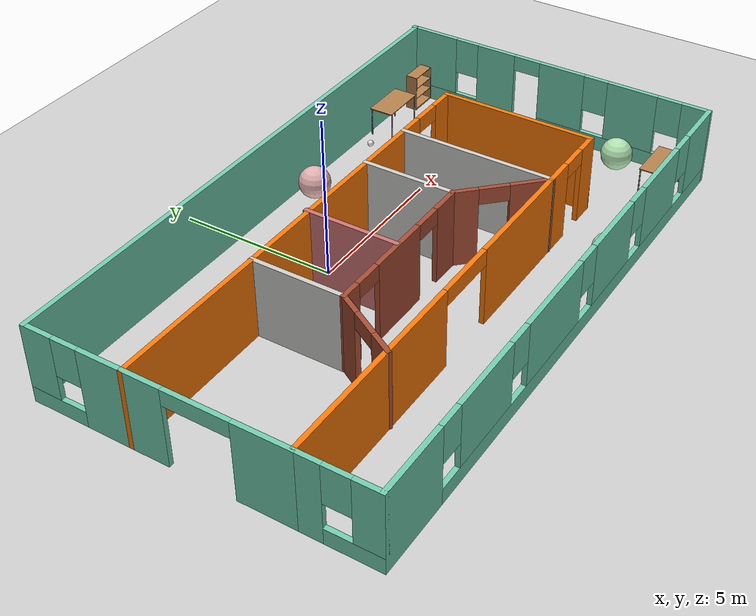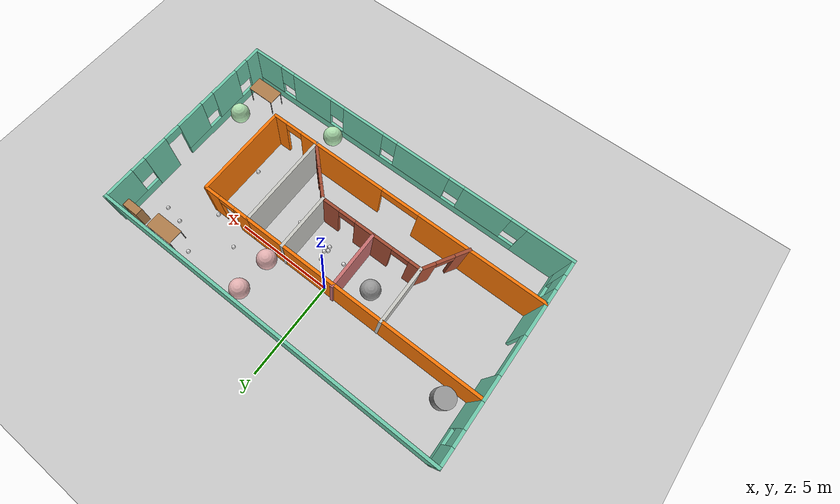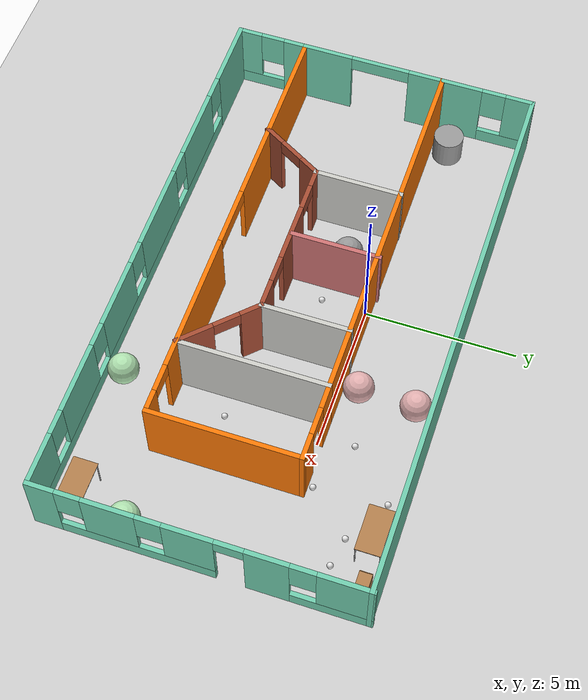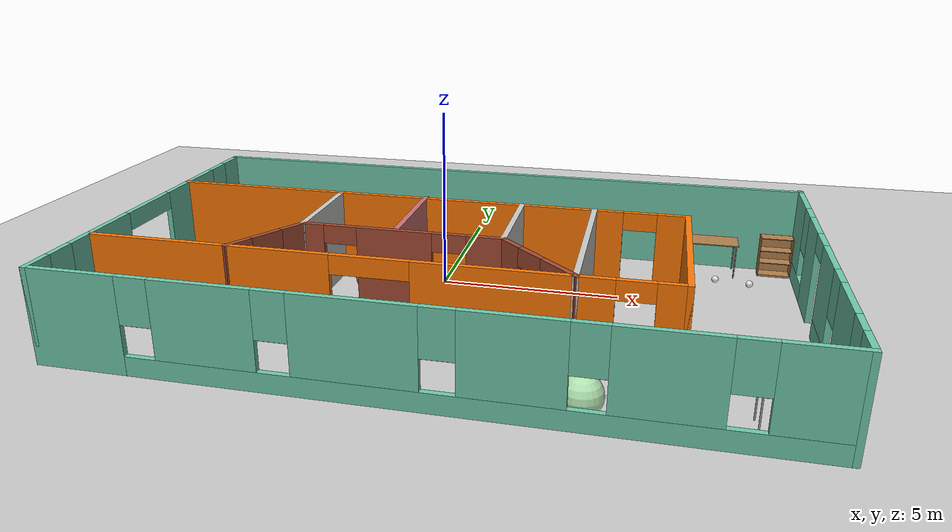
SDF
<sdf version="1.6">
 <world name="default">
  <light name="sun" type="directional">
   <pose>0 0 10 0 -0 0</pose>
   <diffuse>0.8 0.8 0.8 1</diffuse>
   <specular>0.2 0.2 0.2 1</specular>
   <attenuation>
    <range>1000</range>
    <constant>0.9</constant>
    <linear>0.01</linear>
    <quadratic>0.001</quadratic>
   </attenuation>
   <direction>-0.5 0.1 -0.9</direction>
  </light>
  <model name="ground_plane">
   <static>1</static>
   <link name="link">
    <collision name="collision">
     <geometry><plane><normal>0 0 1</normal><size>100 100</size></plane></geometry>
     <surface>
      <contact><collide_bitmask>65535</collide_bitmask></contact>
      <friction><ode><mu>100</mu><mu2>50</mu2></ode></friction>
     </surface>
    </collision>
    <visual name="visual">
     <cast_shadows>0</cast_shadows>
     <geometry><plane><normal>0 0 1</normal><size>100 100</size></plane></geometry>
     <material>
      <script><uri>file://media/materials/scripts/gazebo.material</uri><name>Gazebo/Grey</name></script>
     </material>
    </visual>
   </link>
  </model>
  <gravity>0 0 -9.8</gravity>
  <magnetic_field>6e-06 2.3e-05 -4.2e-05</magnetic_field>
  <atmosphere type="adiabatic"/>
  <physics name="default_physics" default="0" type="ode">
   <max_step_size>0.001</max_step_size>
   <real_time_factor>1</real_time_factor>
   <real_time_update_rate>1000</real_time_update_rate>
  </physics>
  <scene><ambient>0.4 0.4 0.4 1</ambient><background>0.7 0.7 0.7 1</background><shadows>1</shadows></scene>
  <spherical_coordinates>
   <surface_model>EARTH_WGS84</surface_model>
   <latitude_deg>0</latitude_deg>
   <longitude_deg>0</longitude_deg>
   <elevation>0</elevation>
   <heading_deg>0</heading_deg>
  </spherical_coordinates>
  <model name="modelUdacityOffice">
   <pose>0.92 -1.915 0 0 -0 0</pose>
   <link name="Wall_0">
    <collision name="Wall_0_Collision">
     <geometry><box><size>12.5 0.15 2.5</size></box></geometry>
     <pose>0 0 1.25 0 -0 0</pose>
    </collision>
    <visual name="Wall_0_Visual">
     <pose>0 0 1.25 0 -0 0</pose>
     <geometry><box><size>12.5 0.15 2.5</size></box></geometry>
     <material>
      <script><uri>file://media/materials/scripts/gazebo.material</uri><name>Gazebo/Grey</name></script>
      <ambient>0.996078 0.47451 0.0196078 1</ambient>
     </material>
     <meta><layer>0</layer></meta>
    </visual>
    <pose>-2.875 2.025 0 0 -0 3.14159</pose>
   </link>
   <link name="Wall_1">
    <pose>-9.05 -0.4 0 0 -0 -1.5708</pose>
    <visual name="Wall_1_Visual_0">
     <pose>-1.87607 0 1.25 0 -0 0</pose>
     <geometry><box><size>1.24786 0.15 2.5</size></box></geometry>
     <material>
      <script><uri>file://media/materials/scripts/gazebo.material</uri><name>Gazebo/Grey</name></script>
      <ambient>0.435294 0.796078 0.67451 1</ambient>
     </material>
     <meta><layer>0</layer></meta>
    </visual>
    <collision name="Wall_1_Collision_0">
     <geometry><box><size>1.24786 0.15 2.5</size></box></geometry>
     <pose>-1.87607 0 1.25 0 -0 0</pose>
    </collision>
    <visual name="Wall_1_Visual_1">
     <pose>1.62393 0 1.25 0 -0 0</pose>
     <geometry><box><size>1.75214 0.15 2.5</size></box></geometry>
     <material>
      <script><uri>file://media/materials/scripts/gazebo.material</uri><name>Gazebo/Grey</name></script>
      <ambient>0.435294 0.796078 0.67451 1</ambient>
     </material>
     <meta><layer>0</layer></meta>
    </visual>
    <collision name="Wall_1_Collision_1">
     <geometry><box><size>1.75214 0.15 2.5</size></box></geometry>
     <pose>1.62393 0 1.25 0 -0 0</pose>
    </collision>
    <visual name="Wall_1_Visual_2">
     <pose>-0.252138 0 2.25 0 -0 0</pose>
     <geometry><box><size>2 0.15 0.5</size></box></geometry>
     <material>
      <script><uri>file://media/materials/scripts/gazebo.material</uri><name>Gazebo/Grey</name></script>
      <ambient>0.435294 0.796078 0.67451 1</ambient>
     </material>
     <meta><layer>0</layer></meta>
    </visual>
    <collision name="Wall_1_Collision_2">
     <geometry><box><size>2 0.15 0.5</size></box></geometry>
     <pose>-0.252138 0 2.25 0 -0 0</pose>
    </collision>
   </link>
   <link name="Wall_10">
    <collision name="Wall_10_Collision">
     <geometry><box><size>3 0.15 2.5</size></box></geometry>
     <pose>0 0 1.25 0 -0 0</pose>
    </collision>
    <visual name="Wall_10_Visual">
     <pose>0 0 1.25 0 -0 0</pose>
     <geometry><box><size>3 0.15 2.5</size></box></geometry>
     <material>
      <script><uri>file://media/materials/scripts/gazebo.material</uri><name>Gazebo/CeilingTiled</name></script>
      <ambient>1 1 1 1</ambient>
     </material>
     <meta><layer>0</layer></meta>
    </visual>
    <pose>-4.06525 0.615254 0 0 -0 1.5708</pose>
   </link>
   <link name="Wall_12">
    <collision name="Wall_12_Collision">
     <geometry><box><size>3 0.15 2.5</size></box></geometry>
     <pose>0 0 1.25 0 -0 0</pose>
    </collision>
    <visual name="Wall_12_Visual">
     <pose>0 0 1.25 0 -0 0</pose>
     <geometry><box><size>3 0.15 2.5</size></box></geometry>
     <material>
      <script><uri>file://media/materials/scripts/gazebo.material</uri><name>Gazebo/CeilingTiled</name></script>
      <ambient>0.8 0.447059 0.447059 1</ambient>
     </material>
     <meta><layer>0</layer></meta>
    </visual>
    <pose>1.28475 0.615254 0 0 -0 1.5708</pose>
   </link>
   <link name="Wall_18">
    <pose>-9.05 -4 0 0 -0 -1.5708</pose>
    <visual name="Wall_18_Visual_0">
     <pose>-0.830223 0 1.25 0 -0 0</pose>
     <geometry><box><size>0.839555 0.15 2.5</size></box></geometry>
     <material>
      <script><uri>file://media/materials/scripts/gazebo.material</uri><name>Gazebo/Grey</name></script>
      <ambient>0.435294 0.796078 0.67451 1</ambient>
     </material>
     <meta><layer>0</layer></meta>
    </visual>
    <collision name="Wall_18_Collision_0">
     <geometry><box><size>0.839555 0.15 2.5</size></box></geometry>
     <pose>-0.830223 0 1.25 0 -0 0</pose>
    </collision>
    <visual name="Wall_18_Visual_1">
     <pose>0.419777 0 0.25 0 -0 0</pose>
     <geometry><box><size>1.66044 0.15 0.5</size></box></geometry>
     <material>
      <script><uri>file://media/materials/scripts/gazebo.material</uri><name>Gazebo/Grey</name></script>
      <ambient>0.435294 0.796078 0.67451 1</ambient>
     </material>
     <meta><layer>0</layer></meta>
    </visual>
    <collision name="Wall_18_Collision_1">
     <geometry><box><size>1.66044 0.15 0.5</size></box></geometry>
     <pose>0.419777 0 0.25 0 -0 0</pose>
    </collision>
    <visual name="Wall_18_Visual_2">
     <pose>0.819777 0 1.5 0 -0 0</pose>
     <geometry><box><size>0.860445 0.15 2</size></box></geometry>
     <material>
      <script><uri>file://media/materials/scripts/gazebo.material</uri><name>Gazebo/Grey</name></script>
      <ambient>0.435294 0.796078 0.67451 1</ambient>
     </material>
     <meta><layer>0</layer></meta>
    </visual>
    <collision name="Wall_18_Collision_2">
     <geometry><box><size>0.860445 0.15 2</size></box></geometry>
     <pose>0.819777 0 1.5 0 -0 0</pose>
    </collision>
    <visual name="Wall_18_Visual_3">
     <pose>-0.010445 0 1.9 0 -0 0</pose>
     <geometry><box><size>0.8 0.15 1.2</size></box></geometry>
     <material>
      <script><uri>file://media/materials/scripts/gazebo.material</uri><name>Gazebo/Grey</name></script>
      <ambient>0.435294 0.796078 0.67451 1</ambient>
     </material>
     <meta><layer>0</layer></meta>
    </visual>
    <collision name="Wall_18_Collision_3">
     <geometry><box><size>0.8 0.15 1.2</size></box></geometry>
     <pose>-0.010445 0 1.9 0 -0 0</pose>
    </collision>
   </link>
   <link name="Wall_19">
    <pose>-0 -5.175 0 0 -0 0</pose>
    <visual name="Wall_19_Visual_0">
     <pose>-7.92331 0 1.25 0 -0 0</pose>
     <geometry><box><size>2.40337 0.15 2.5</size></box></geometry>
     <material>
      <script><uri>file://media/materials/scripts/gazebo.material</uri><name>Gazebo/Grey</name></script>
      <ambient>0.435294 0.796078 0.67451 1</ambient>
     </material>
     <meta><layer>0</layer></meta>
    </visual>
    <collision name="Wall_19_Collision_0">
     <geometry><box><size>2.40337 0.15 2.5</size></box></geometry>
     <pose>-7.92331 0 1.25 0 -0 0</pose>
    </collision>
    <visual name="Wall_19_Visual_1">
     <pose>1.20168 0 0.25 0 -0 0</pose>
     <geometry><box><size>15.8466 0.15 0.5</size></box></geometry>
     <material>
      <script><uri>file://media/materials/scripts/gazebo.material</uri><name>Gazebo/Grey</name></script>
      <ambient>0.435294 0.796078 0.67451 1</ambient>
     </material>
     <meta><layer>0</layer></meta>
    </visual>
    <collision name="Wall_19_Collision_1">
     <geometry><box><size>15.8466 0.15 0.5</size></box></geometry>
     <pose>1.20168 0 0.25 0 -0 0</pose>
    </collision>
    <visual name="Wall_19_Visual_2">
     <pose>-4.67232 0 1.5 0 -0 0</pose>
     <geometry><box><size>2.49863 0.15 2</size></box></geometry>
     <material>
      <script><uri>file://media/materials/scripts/gazebo.material</uri><name>Gazebo/Grey</name></script>
      <ambient>0.435294 0.796078 0.67451 1</ambient>
     </material>
     <meta><layer>0</layer></meta>
    </visual>
    <collision name="Wall_19_Collision_2">
     <geometry><box><size>2.49863 0.15 2</size></box></geometry>
     <pose>-4.67232 0 1.5 0 -0 0</pose>
    </collision>
    <visual name="Wall_19_Visual_3">
     <pose>-1.15244 0 1.5 0 -0 0</pose>
     <geometry><box><size>2.94112 0.15 2</size></box></geometry>
     <material>
      <script><uri>file://media/materials/scripts/gazebo.material</uri><name>Gazebo/Grey</name></script>
      <ambient>0.435294 0.796078 0.67451 1</ambient>
     </material>
     <meta><layer>0</layer></meta>
    </visual>
    <collision name="Wall_19_Collision_3">
     <geometry><box><size>2.94112 0.15 2</size></box></geometry>
     <pose>-1.15244 0 1.5 0 -0 0</pose>
    </collision>
    <visual name="Wall_19_Visual_4">
     <pose>2.28698 0 1.5 0 -0 0</pose>
     <geometry><box><size>2.33772 0.15 2</size></box></geometry>
     <material>
      <script><uri>file://media/materials/scripts/gazebo.material</uri><name>Gazebo/Grey</name></script>
      <ambient>0.435294 0.796078 0.67451 1</ambient>
     </material>
     <meta><layer>0</layer></meta>
    </visual>
    <collision name="Wall_19_Collision_4">
     <geometry><box><size>2.33772 0.15 2</size></box></geometry>
     <pose>2.28698 0 1.5 0 -0 0</pose>
    </collision>
    <visual name="Wall_19_Visual_5">
     <pose>5.4247 0 1.5 0 -0 0</pose>
     <geometry><box><size>2.33772 0.15 2</size></box></geometry>
     <material>
      <script><uri>file://media/materials/scripts/gazebo.material</uri><name>Gazebo/Grey</name></script>
      <ambient>0.435294 0.796078 0.67451 1</ambient>
     </material>
     <meta><layer>0</layer></meta>
    </visual>
    <collision name="Wall_19_Collision_5">
     <geometry><box><size>2.33772 0.15 2</size></box></geometry>
     <pose>5.4247 0 1.5 0 -0 0</pose>
    </collision>
    <visual name="Wall_19_Visual_6">
     <pose>8.25928 0 1.5 0 -0 0</pose>
     <geometry><box><size>1.73144 0.15 2</size></box></geometry>
     <material>
      <script><uri>file://media/materials/scripts/gazebo.material</uri><name>Gazebo/Grey</name></script>
      <ambient>0.435294 0.796078 0.67451 1</ambient>
     </material>
     <meta><layer>0</layer></meta>
    </visual>
    <collision name="Wall_19_Collision_6">
     <geometry><box><size>1.73144 0.15 2</size></box></geometry>
     <pose>8.25928 0 1.5 0 -0 0</pose>
    </collision>
    <visual name="Wall_19_Visual_7">
     <pose>-6.32163 0 1.9 0 -0 0</pose>
     <geometry><box><size>0.8 0.15 1.2</size></box></geometry>
     <material>
      <script><uri>file://media/materials/scripts/gazebo.material</uri><name>Gazebo/Grey</name></script>
      <ambient>0.435294 0.796078 0.67451 1</ambient>
     </material>
     <meta><layer>0</layer></meta>
    </visual>
    <collision name="Wall_19_Collision_7">
     <geometry><box><size>0.8 0.15 1.2</size></box></geometry>
     <pose>-6.32163 0 1.9 0 -0 0</pose>
    </collision>
    <visual name="Wall_19_Visual_8">
     <pose>-3.023 0 1.9 0 -0 0</pose>
     <geometry><box><size>0.8 0.15 1.2</size></box></geometry>
     <material>
      <script><uri>file://media/materials/scripts/gazebo.material</uri><name>Gazebo/Grey</name></script>
      <ambient>0.435294 0.796078 0.67451 1</ambient>
     </material>
     <meta><layer>0</layer></meta>
    </visual>
    <collision name="Wall_19_Collision_8">
     <geometry><box><size>0.8 0.15 1.2</size></box></geometry>
     <pose>-3.023 0 1.9 0 -0 0</pose>
    </collision>
    <visual name="Wall_19_Visual_9">
     <pose>0.71812 0 1.9 0 -0 0</pose>
     <geometry><box><size>0.8 0.15 1.2</size></box></geometry>
     <material>
      <script><uri>file://media/materials/scripts/gazebo.material</uri><name>Gazebo/Grey</name></script>
      <ambient>0.435294 0.796078 0.67451 1</ambient>
     </material>
     <meta><layer>0</layer></meta>
    </visual>
    <collision name="Wall_19_Collision_9">
     <geometry><box><size>0.8 0.15 1.2</size></box></geometry>
     <pose>0.71812 0 1.9 0 -0 0</pose>
    </collision>
    <visual name="Wall_19_Visual_10">
     <pose>3.85584 0 1.9 0 -0 0</pose>
     <geometry><box><size>0.8 0.15 1.2</size></box></geometry>
     <material>
      <script><uri>file://media/materials/scripts/gazebo.material</uri><name>Gazebo/Grey</name></script>
      <ambient>0.435294 0.796078 0.67451 1</ambient>
     </material>
     <meta><layer>0</layer></meta>
    </visual>
    <collision name="Wall_19_Collision_10">
     <geometry><box><size>0.8 0.15 1.2</size></box></geometry>
     <pose>3.85584 0 1.9 0 -0 0</pose>
    </collision>
    <visual name="Wall_19_Visual_11">
     <pose>6.99355 0 1.9 0 -0 0</pose>
     <geometry><box><size>0.8 0.15 1.2</size></box></geometry>
     <material>
      <script><uri>file://media/materials/scripts/gazebo.material</uri><name>Gazebo/Grey</name></script>
      <ambient>0.435294 0.796078 0.67451 1</ambient>
     </material>
     <meta><layer>0</layer></meta>
    </visual>
    <collision name="Wall_19_Collision_11">
     <geometry><box><size>0.8 0.15 1.2</size></box></geometry>
     <pose>6.99355 0 1.9 0 -0 0</pose>
    </collision>
   </link>
   <link name="Wall_2">
    <pose>-1.625 -2.825 0 0 -0 0</pose>
    <visual name="Wall_2_Visual_0">
     <pose>-4.21486 0 1.25 0 -0 0</pose>
     <geometry><box><size>6.57029 0.15 2.5</size></box></geometry>
     <material>
      <script><uri>file://media/materials/scripts/gazebo.material</uri><name>Gazebo/Grey</name></script>
      <ambient>0.996078 0.47451 0.0196078 1</ambient>
     </material>
     <meta><layer>0</layer></meta>
    </visual>
    <collision name="Wall_2_Collision_0">
     <geometry><box><size>6.57029 0.15 2.5</size></box></geometry>
     <pose>-4.21486 0 1.25 0 -0 0</pose>
    </collision>
    <visual name="Wall_2_Visual_1">
     <pose>3.44278 0 1.25 0 -0 0</pose>
     <geometry><box><size>4.74498 0.15 2.5</size></box></geometry>
     <material>
      <script><uri>file://media/materials/scripts/gazebo.material</uri><name>Gazebo/Grey</name></script>
      <ambient>0.996078 0.47451 0.0196078 1</ambient>
     </material>
     <meta><layer>0</layer></meta>
    </visual>
    <collision name="Wall_2_Collision_1">
     <geometry><box><size>4.74498 0.15 2.5</size></box></geometry>
     <pose>3.44278 0 1.25 0 -0 0</pose>
    </collision>
    <visual name="Wall_2_Visual_2">
     <pose>7.10763 0 1.25 0 -0 0</pose>
     <geometry><box><size>0.784733 0.15 2.5</size></box></geometry>
     <material>
      <script><uri>file://media/materials/scripts/gazebo.material</uri><name>Gazebo/Grey</name></script>
      <ambient>0.996078 0.47451 0.0196078 1</ambient>
     </material>
     <meta><layer>0</layer></meta>
    </visual>
    <collision name="Wall_2_Collision_2">
     <geometry><box><size>0.784733 0.15 2.5</size></box></geometry>
     <pose>7.10763 0 1.25 0 -0 0</pose>
    </collision>
    <visual name="Wall_2_Visual_3">
     <pose>0.070287 0 2.25 0 -0 0</pose>
     <geometry><box><size>2 0.15 0.5</size></box></geometry>
     <material>
      <script><uri>file://media/materials/scripts/gazebo.material</uri><name>Gazebo/Grey</name></script>
      <ambient>0.996078 0.47451 0.0196078 1</ambient>
     </material>
     <meta><layer>0</layer></meta>
    </visual>
    <collision name="Wall_2_Collision_3">
     <geometry><box><size>2 0.15 0.5</size></box></geometry>
     <pose>0.070287 0 2.25 0 -0 0</pose>
    </collision>
    <visual name="Wall_2_Visual_4">
     <pose>6.26527 0 2.25 0 -0 0</pose>
     <geometry><box><size>0.9 0.15 0.5</size></box></geometry>
     <material>
      <script><uri>file://media/materials/scripts/gazebo.material</uri><name>Gazebo/Grey</name></script>
      <ambient>0.996078 0.47451 0.0196078 1</ambient>
     </material>
     <meta><layer>0</layer></meta>
    </visual>
    <collision name="Wall_2_Collision_4">
     <geometry><box><size>0.9 0.15 0.5</size></box></geometry>
     <pose>6.26527 0 2.25 0 -0 0</pose>
    </collision>
   </link>
   <link name="Wall_20">
    <pose>9.05 0 0 0 -0 1.5708</pose>
    <visual name="Wall_20_Visual_0">
     <pose>-4.78961 0 1.25 0 -0 0</pose>
     <geometry><box><size>0.920786 0.15 2.5</size></box></geometry>
     <material>
      <script><uri>file://media/materials/scripts/gazebo.material</uri><name>Gazebo/Grey</name></script>
      <ambient>0.435294 0.796078 0.67451 1</ambient>
     </material>
     <meta><layer>0</layer></meta>
    </visual>
    <collision name="Wall_20_Collision_0">
     <geometry><box><size>0.920786 0.15 2.5</size></box></geometry>
     <pose>-4.78961 0 1.25 0 -0 0</pose>
    </collision>
    <visual name="Wall_20_Visual_1">
     <pose>2.05946 0 1.25 0 -0 0</pose>
     <geometry><box><size>1.34238 0.15 2.5</size></box></geometry>
     <material>
      <script><uri>file://media/materials/scripts/gazebo.material</uri><name>Gazebo/Grey</name></script>
      <ambient>0.435294 0.796078 0.67451 1</ambient>
     </material>
     <meta><layer>0</layer></meta>
    </visual>
    <collision name="Wall_20_Collision_1">
     <geometry><box><size>1.34238 0.15 2.5</size></box></geometry>
     <pose>2.05946 0 1.25 0 -0 0</pose>
    </collision>
    <visual name="Wall_20_Visual_2">
     <pose>-1.92047 0 0.25 0 -0 0</pose>
     <geometry><box><size>4.81748 0.15 0.5</size></box></geometry>
     <material>
      <script><uri>file://media/materials/scripts/gazebo.material</uri><name>Gazebo/Grey</name></script>
      <ambient>0.435294 0.796078 0.67451 1</ambient>
     </material>
     <meta><layer>0</layer></meta>
    </visual>
    <collision name="Wall_20_Collision_2">
     <geometry><box><size>4.81748 0.15 0.5</size></box></geometry>
     <pose>-1.92047 0 0.25 0 -0 0</pose>
    </collision>
    <visual name="Wall_20_Visual_3">
     <pose>3.99032 0 0.25 0 -0 0</pose>
     <geometry><box><size>2.51935 0.15 0.5</size></box></geometry>
     <material>
      <script><uri>file://media/materials/scripts/gazebo.material</uri><name>Gazebo/Grey</name></script>
      <ambient>0.435294 0.796078 0.67451 1</ambient>
     </material>
     <meta><layer>0</layer></meta>
    </visual>
    <collision name="Wall_20_Collision_3">
     <geometry><box><size>2.51935 0.15 0.5</size></box></geometry>
     <pose>3.99032 0 0.25 0 -0 0</pose>
    </collision>
    <visual name="Wall_20_Visual_4">
     <pose>-2.70229 0 1.5 0 -0 0</pose>
     <geometry><box><size>1.65386 0.15 2</size></box></geometry>
     <material>
      <script><uri>file://media/materials/scripts/gazebo.material</uri><name>Gazebo/Grey</name></script>
      <ambient>0.435294 0.796078 0.67451 1</ambient>
     </material>
     <meta><layer>0</layer></meta>
    </visual>
    <collision name="Wall_20_Collision_4">
     <geometry><box><size>1.65386 0.15 2</size></box></geometry>
     <pose>-2.70229 0 1.5 0 -0 0</pose>
    </collision>
    <visual name="Wall_20_Visual_5">
     <pose>-0.293544 0 1.5 0 -0 0</pose>
     <geometry><box><size>1.56363 0.15 2</size></box></geometry>
     <material>
      <script><uri>file://media/materials/scripts/gazebo.material</uri><name>Gazebo/Grey</name></script>
      <ambient>0.435294 0.796078 0.67451 1</ambient>
     </material>
     <meta><layer>0</layer></meta>
    </visual>
    <collision name="Wall_20_Collision_5">
     <geometry><box><size>1.56363 0.15 2</size></box></geometry>
     <pose>-0.293544 0 1.5 0 -0 0</pose>
    </collision>
    <visual name="Wall_20_Visual_6">
     <pose>-0.293544 0 1.5 0 -0 0</pose>
     <geometry><box><size>1.56363 0.15 2</size></box></geometry>
     <material>
      <script><uri>file://media/materials/scripts/gazebo.material</uri><name>Gazebo/Grey</name></script>
      <ambient>0.435294 0.796078 0.67451 1</ambient>
     </material>
     <meta><layer>0</layer></meta>
    </visual>
    <collision name="Wall_20_Collision_6">
     <geometry><box><size>1.56363 0.15 2</size></box></geometry>
     <pose>-0.293544 0 1.5 0 -0 0</pose>
    </collision>
    <visual name="Wall_20_Visual_7">
     <pose>4.39032 0 1.5 0 -0 0</pose>
     <geometry><box><size>1.71935 0.15 2</size></box></geometry>
     <material>
      <script><uri>file://media/materials/scripts/gazebo.material</uri><name>Gazebo/Grey</name></script>
      <ambient>0.435294 0.796078 0.67451 1</ambient>
     </material>
     <meta><layer>0</layer></meta>
    </visual>
    <collision name="Wall_20_Collision_7">
     <geometry><box><size>1.71935 0.15 2</size></box></geometry>
     <pose>4.39032 0 1.5 0 -0 0</pose>
    </collision>
    <visual name="Wall_20_Visual_8">
     <pose>-3.92921 0 1.9 0 -0 0</pose>
     <geometry><box><size>0.8 0.15 1.2</size></box></geometry>
     <material>
      <script><uri>file://media/materials/scripts/gazebo.material</uri><name>Gazebo/Grey</name></script>
      <ambient>0.435294 0.796078 0.67451 1</ambient>
     </material>
     <meta><layer>0</layer></meta>
    </visual>
    <collision name="Wall_20_Collision_8">
     <geometry><box><size>0.8 0.15 1.2</size></box></geometry>
     <pose>-3.92921 0 1.9 0 -0 0</pose>
    </collision>
    <visual name="Wall_20_Visual_9">
     <pose>3.13065 0 1.9 0 -0 0</pose>
     <geometry><box><size>0.8 0.15 1.2</size></box></geometry>
     <material>
      <script><uri>file://media/materials/scripts/gazebo.material</uri><name>Gazebo/Grey</name></script>
      <ambient>0.435294 0.796078 0.67451 1</ambient>
     </material>
     <meta><layer>0</layer></meta>
    </visual>
    <collision name="Wall_20_Collision_9">
     <geometry><box><size>0.8 0.15 1.2</size></box></geometry>
     <pose>3.13065 0 1.9 0 -0 0</pose>
    </collision>
    <visual name="Wall_20_Visual_10">
     <pose>-1.47536 0 1.9 0 -0 0</pose>
     <geometry><box><size>0.8 0.15 1.2</size></box></geometry>
     <material>
      <script><uri>file://media/materials/scripts/gazebo.material</uri><name>Gazebo/Grey</name></script>
      <ambient>0.435294 0.796078 0.67451 1</ambient>
     </material>
     <meta><layer>0</layer></meta>
    </visual>
    <collision name="Wall_20_Collision_10">
     <geometry><box><size>0.8 0.15 1.2</size></box></geometry>
     <pose>-1.47536 0 1.9 0 -0 0</pose>
    </collision>
    <visual name="Wall_20_Visual_11">
     <pose>0.93827 0 2.25 0 -0 0</pose>
     <geometry><box><size>0.9 0.15 0.5</size></box></geometry>
     <material>
      <script><uri>file://media/materials/scripts/gazebo.material</uri><name>Gazebo/Grey</name></script>
      <ambient>0.435294 0.796078 0.67451 1</ambient>
     </material>
     <meta><layer>0</layer></meta>
    </visual>
    <collision name="Wall_20_Collision_11">
     <geometry><box><size>0.9 0.15 0.5</size></box></geometry>
     <pose>0.93827 0 2.25 0 -0 0</pose>
    </collision>
    <visual name="Wall_20_Visual_12">
     <pose>0.93827 0 2.25 0 -0 0</pose>
     <geometry><box><size>0.9 0.15 0.5</size></box></geometry>
     <material>
      <script><uri>file://media/materials/scripts/gazebo.material</uri><name>Gazebo/Grey</name></script>
      <ambient>0.435294 0.796078 0.67451 1</ambient>
     </material>
     <meta><layer>0</layer></meta>
    </visual>
    <collision name="Wall_20_Collision_12">
     <geometry><box><size>0.9 0.15 0.5</size></box></geometry>
     <pose>0.93827 0 2.25 0 -0 0</pose>
    </collision>
   </link>
   <link name="Wall_24">
    <pose>-9.05 3.575 0 0 -0 1.5708</pose>
    <visual name="Wall_24_Visual_0">
     <pose>-0.892744 0 1.25 0 -0 0</pose>
     <geometry><box><size>1.46451 0.15 2.5</size></box></geometry>
     <material>
      <script><uri>file://media/materials/scripts/gazebo.material</uri><name>Gazebo/Grey</name></script>
      <ambient>0.435294 0.796078 0.67451 1</ambient>
     </material>
     <meta><layer>0</layer></meta>
    </visual>
    <collision name="Wall_24_Collision_0">
     <geometry><box><size>1.46451 0.15 2.5</size></box></geometry>
     <pose>-0.892744 0 1.25 0 -0 0</pose>
    </collision>
    <visual name="Wall_24_Visual_1">
     <pose>0.732256 0 0.25 0 -0 0</pose>
     <geometry><box><size>1.78549 0.15 0.5</size></box></geometry>
     <material>
      <script><uri>file://media/materials/scripts/gazebo.material</uri><name>Gazebo/Grey</name></script>
      <ambient>0.435294 0.796078 0.67451 1</ambient>
     </material>
     <meta><layer>0</layer></meta>
    </visual>
    <collision name="Wall_24_Collision_1">
     <geometry><box><size>1.78549 0.15 0.5</size></box></geometry>
     <pose>0.732256 0 0.25 0 -0 0</pose>
    </collision>
    <visual name="Wall_24_Visual_2">
     <pose>1.13226 0 1.5 0 -0 0</pose>
     <geometry><box><size>0.985489 0.15 2</size></box></geometry>
     <material>
      <script><uri>file://media/materials/scripts/gazebo.material</uri><name>Gazebo/Grey</name></script>
      <ambient>0.435294 0.796078 0.67451 1</ambient>
     </material>
     <meta><layer>0</layer></meta>
    </visual>
    <collision name="Wall_24_Collision_2">
     <geometry><box><size>0.985489 0.15 2</size></box></geometry>
     <pose>1.13226 0 1.5 0 -0 0</pose>
    </collision>
    <visual name="Wall_24_Visual_3">
     <pose>0.239511 0 1.9 0 -0 0</pose>
     <geometry><box><size>0.8 0.15 1.2</size></box></geometry>
     <material>
      <script><uri>file://media/materials/scripts/gazebo.material</uri><name>Gazebo/Grey</name></script>
      <ambient>0.435294 0.796078 0.67451 1</ambient>
     </material>
     <meta><layer>0</layer></meta>
    </visual>
    <collision name="Wall_24_Collision_3">
     <geometry><box><size>0.8 0.15 1.2</size></box></geometry>
     <pose>0.239511 0 1.9 0 -0 0</pose>
    </collision>
   </link>
   <link name="Wall_25">
    <collision name="Wall_25_Collision">
     <geometry><box><size>18.25 0.15 2.5</size></box></geometry>
     <pose>0 0 1.25 0 -0 0</pose>
    </collision>
    <visual name="Wall_25_Visual">
     <pose>0 0 1.25 0 -0 0</pose>
     <geometry><box><size>18.25 0.15 2.5</size></box></geometry>
     <material>
      <script><uri>file://media/materials/scripts/gazebo.material</uri><name>Gazebo/Grey</name></script>
      <ambient>0.435294 0.796078 0.67451 1</ambient>
     </material>
     <meta><layer>0</layer></meta>
    </visual>
    <pose>-0 5.125 0 0 -0 0</pose>
   </link>
   <link name="Wall_27">
    <collision name="Wall_27_Collision">
     <geometry><box><size>3 0.15 2.5</size></box></geometry>
     <pose>0 0 1.25 0 -0 0</pose>
    </collision>
    <visual name="Wall_27_Visual">
     <pose>0 0 1.25 0 -0 0</pose>
     <geometry><box><size>3 0.15 2.5</size></box></geometry>
     <material>
      <script><uri>file://media/materials/scripts/gazebo.material</uri><name>Gazebo/Grey</name></script>
      <ambient>0.8 0.447059 0.447059 1</ambient>
     </material>
     <meta><layer>0</layer></meta>
    </visual>
    <pose>-1.5346 0.67373 0 0 -0 1.5708</pose>
   </link>
   <link name="Wall_3">
    <collision name="Wall_3_Collision">
     <geometry><box><size>5 0.15 2.5</size></box></geometry>
     <pose>0 0 1.25 0 -0 0</pose>
    </collision>
    <visual name="Wall_3_Visual">
     <pose>0 0 1.25 0 -0 0</pose>
     <geometry><box><size>5 0.15 2.5</size></box></geometry>
     <material>
      <script><uri>file://media/materials/scripts/gazebo.material</uri><name>Gazebo/Grey</name></script>
      <ambient>0.996078 0.47451 0.0196078 1</ambient>
     </material>
     <meta><layer>0</layer></meta>
    </visual>
    <pose>5.8 -0.4 0 0 -0 1.5708</pose>
   </link>
   <link name="Wall_4">
    <pose>4.55 2.025 0 0 -0 3.14159</pose>
    <visual name="Wall_4_Visual_0">
     <pose>-0.88235 0 1.25 0 -0 0</pose>
     <geometry><box><size>0.885301 0.15 2.5</size></box></geometry>
     <material>
      <script><uri>file://media/materials/scripts/gazebo.material</uri><name>Gazebo/Grey</name></script>
      <ambient>0.996078 0.47451 0.0196078 1</ambient>
     </material>
     <meta><layer>0</layer></meta>
    </visual>
    <collision name="Wall_4_Collision_0">
     <geometry><box><size>0.885301 0.15 2.5</size></box></geometry>
     <pose>-0.88235 0 1.25 0 -0 0</pose>
    </collision>
    <visual name="Wall_4_Visual_1">
     <pose>0.89265 0 1.25 0 -0 0</pose>
     <geometry><box><size>0.864699 0.15 2.5</size></box></geometry>
     <material>
      <script><uri>file://media/materials/scripts/gazebo.material</uri><name>Gazebo/Grey</name></script>
      <ambient>0.996078 0.47451 0.0196078 1</ambient>
     </material>
     <meta><layer>0</layer></meta>
    </visual>
    <collision name="Wall_4_Collision_1">
     <geometry><box><size>0.864699 0.15 2.5</size></box></geometry>
     <pose>0.89265 0 1.25 0 -0 0</pose>
    </collision>
    <visual name="Wall_4_Visual_2">
     <pose>0.010301 0 2.25 0 -0 0</pose>
     <geometry><box><size>0.9 0.15 0.5</size></box></geometry>
     <material>
      <script><uri>file://media/materials/scripts/gazebo.material</uri><name>Gazebo/Grey</name></script>
      <ambient>0.996078 0.47451 0.0196078 1</ambient>
     </material>
     <meta><layer>0</layer></meta>
    </visual>
    <collision name="Wall_4_Collision_2">
     <geometry><box><size>0.9 0.15 0.5</size></box></geometry>
     <pose>0.010301 0 2.25 0 -0 0</pose>
    </collision>
   </link>
   <link name="Wall_5">
    <collision name="Wall_5_Collision">
     <geometry><box><size>5 0.15 2.5</size></box></geometry>
     <pose>0 0 1.25 0 -0 0</pose>
    </collision>
    <visual name="Wall_5_Visual">
     <pose>0 0 1.25 0 -0 0</pose>
     <geometry><box><size>5 0.15 2.5</size></box></geometry>
     <material>
      <script><uri>file://media/materials/scripts/gazebo.material</uri><name>Gazebo/CeilingTiled</name></script>
      <ambient>1 1 1 1</ambient>
     </material>
     <meta><layer>0</layer></meta>
    </visual>
    <pose>3.3 -0.4 0 0 -0 -1.5708</pose>
   </link>
   <link name="Wall_6">
    <pose>2.29237 -1.81737 0 0 -0 2.35619</pose>
    <visual name="Wall_6_Visual_0">
     <pose>-0.852173 0 1.25 0 -0 0</pose>
     <geometry><box><size>1.29566 0.15 2.5</size></box></geometry>
     <material>
      <script><uri>file://media/materials/scripts/gazebo.material</uri><name>Gazebo/Bricks</name></script>
      <ambient>1 1 1 1</ambient>
     </material>
     <meta><layer>0</layer></meta>
    </visual>
    <collision name="Wall_6_Collision_0">
     <geometry><box><size>1.29566 0.15 2.5</size></box></geometry>
     <pose>-0.852173 0 1.25 0 -0 0</pose>
    </collision>
    <visual name="Wall_6_Visual_1">
     <pose>1.09783 0 1.25 0 -0 0</pose>
     <geometry><box><size>0.804345 0.15 2.5</size></box></geometry>
     <material>
      <script><uri>file://media/materials/scripts/gazebo.material</uri><name>Gazebo/Bricks</name></script>
      <ambient>1 1 1 1</ambient>
     </material>
     <meta><layer>0</layer></meta>
    </visual>
    <collision name="Wall_6_Collision_1">
     <geometry><box><size>0.804345 0.15 2.5</size></box></geometry>
     <pose>1.09783 0 1.25 0 -0 0</pose>
    </collision>
    <visual name="Wall_6_Visual_2">
     <pose>0.245655 0 2.25 0 -0 0</pose>
     <geometry><box><size>0.9 0.15 0.5</size></box></geometry>
     <material>
      <script><uri>file://media/materials/scripts/gazebo.material</uri><name>Gazebo/Bricks</name></script>
      <ambient>1 1 1 1</ambient>
     </material>
     <meta><layer>0</layer></meta>
    </visual>
    <collision name="Wall_6_Collision_2">
     <geometry><box><size>0.9 0.15 0.5</size></box></geometry>
     <pose>0.245655 0 2.25 0 -0 0</pose>
    </collision>
   </link>
   <link name="Wall_7">
    <pose>-1.39025 -0.809746 0 0 -0 3.14159</pose>
    <visual name="Wall_7_Visual_0">
     <pose>-2.24186 0 1.25 0 -0 0</pose>
     <geometry><box><size>1.01628 0.15 2.5</size></box></geometry>
     <material>
      <script><uri>file://media/materials/scripts/gazebo.material</uri><name>Gazebo/Bricks</name></script>
      <ambient>1 1 1 1</ambient>
     </material>
     <meta><layer>0</layer></meta>
    </visual>
    <collision name="Wall_7_Collision_0">
     <geometry><box><size>1.01628 0.15 2.5</size></box></geometry>
     <pose>-2.24186 0 1.25 0 -0 0</pose>
    </collision>
    <visual name="Wall_7_Visual_1">
     <pose>0.174516 0 1.25 0 -0 0</pose>
     <geometry><box><size>2.01647 0.15 2.5</size></box></geometry>
     <material>
      <script><uri>file://media/materials/scripts/gazebo.material</uri><name>Gazebo/Bricks</name></script>
      <ambient>1 1 1 1</ambient>
     </material>
     <meta><layer>0</layer></meta>
    </visual>
    <collision name="Wall_7_Collision_1">
     <geometry><box><size>2.01647 0.15 2.5</size></box></geometry>
     <pose>0.174516 0 1.25 0 -0 0</pose>
    </collision>
    <visual name="Wall_7_Visual_2">
     <pose>2.41637 0 1.25 0 -0 0</pose>
     <geometry><box><size>0.66725 0.15 2.5</size></box></geometry>
     <material>
      <script><uri>file://media/materials/scripts/gazebo.material</uri><name>Gazebo/Bricks</name></script>
      <ambient>1 1 1 1</ambient>
     </material>
     <meta><layer>0</layer></meta>
    </visual>
    <collision name="Wall_7_Collision_2">
     <geometry><box><size>0.66725 0.15 2.5</size></box></geometry>
     <pose>2.41637 0 1.25 0 -0 0</pose>
    </collision>
    <visual name="Wall_7_Visual_3">
     <pose>-1.28372 0 2.25 0 -0 0</pose>
     <geometry><box><size>0.9 0.15 0.5</size></box></geometry>
     <material>
      <script><uri>file://media/materials/scripts/gazebo.material</uri><name>Gazebo/Bricks</name></script>
      <ambient>1 1 1 1</ambient>
     </material>
     <meta><layer>0</layer></meta>
    </visual>
    <collision name="Wall_7_Collision_3">
     <geometry><box><size>0.9 0.15 0.5</size></box></geometry>
     <pose>-1.28372 0 2.25 0 -0 0</pose>
    </collision>
    <visual name="Wall_7_Visual_4">
     <pose>1.63275 0 2.25 0 -0 0</pose>
     <geometry><box><size>0.9 0.15 0.5</size></box></geometry>
     <material>
      <script><uri>file://media/materials/scripts/gazebo.material</uri><name>Gazebo/Bricks</name></script>
      <ambient>1 1 1 1</ambient>
     </material>
     <meta><layer>0</layer></meta>
    </visual>
    <collision name="Wall_7_Collision_4">
     <geometry><box><size>0.9 0.15 0.5</size></box></geometry>
     <pose>1.63275 0 2.25 0 -0 0</pose>
    </collision>
   </link>
   <link name="Wall_8">
    <pose>-4.65275 -1.82733 0 0 -0 -2.0944</pose>
    <visual name="Wall_8_Visual_0">
     <pose>-0.851164 0 1.25 0 -0 0</pose>
     <geometry><box><size>0.797673 0.15 2.5</size></box></geometry>
     <material>
      <script><uri>file://media/materials/scripts/gazebo.material</uri><name>Gazebo/Bricks</name></script>
      <ambient>1 1 1 1</ambient>
     </material>
     <meta><layer>0</layer></meta>
    </visual>
    <collision name="Wall_8_Collision_0">
     <geometry><box><size>0.797673 0.15 2.5</size></box></geometry>
     <pose>-0.851164 0 1.25 0 -0 0</pose>
    </collision>
    <visual name="Wall_8_Visual_1">
     <pose>0.848836 0 1.25 0 -0 0</pose>
     <geometry><box><size>0.802327 0.15 2.5</size></box></geometry>
     <material>
      <script><uri>file://media/materials/scripts/gazebo.material</uri><name>Gazebo/Bricks</name></script>
      <ambient>1 1 1 1</ambient>
     </material>
     <meta><layer>0</layer></meta>
    </visual>
    <collision name="Wall_8_Collision_1">
     <geometry><box><size>0.802327 0.15 2.5</size></box></geometry>
     <pose>0.848836 0 1.25 0 -0 0</pose>
    </collision>
    <visual name="Wall_8_Visual_2">
     <pose>-0.002327 0 2.25 0 -0 0</pose>
     <geometry><box><size>0.9 0.15 0.5</size></box></geometry>
     <material>
      <script><uri>file://media/materials/scripts/gazebo.material</uri><name>Gazebo/Bricks</name></script>
      <ambient>1 1 1 1</ambient>
     </material>
     <meta><layer>0</layer></meta>
    </visual>
    <collision name="Wall_8_Collision_2">
     <geometry><box><size>0.9 0.15 0.5</size></box></geometry>
     <pose>-0.002327 0 2.25 0 -0 0</pose>
    </collision>
   </link>
   <static>1</static>
  </model>
  <model name="bookshelf">
   <static>1</static>
   <link name="link">
    <inertial><mass>1</mass></inertial>
    <collision name="back">
     <pose>0 0.005 0.6 0 -0 0</pose>
     <geometry><box><size>0.9 0.01 1.2</size></box></geometry>
    </collision>
    <visual name="visual1">
     <pose>0 0.005 0.6 0 -0 0</pose>
     <geometry><box><size>0.9 0.01 1.2</size></box></geometry>
     <material>
      <script><uri>file://media/materials/scripts/gazebo.material</uri><name>Gazebo/Wood</name></script>
     </material>
    </visual>
    <collision name="left_side">
     <pose>0.45 -0.195 0.6 0 -0 0</pose>
     <geometry><box><size>0.02 0.4 1.2</size></box></geometry>
    </collision>
    <visual name="visual2">
     <pose>0.45 -0.195 0.6 0 -0 0</pose>
     <geometry><box><size>0.02 0.4 1.2</size></box></geometry>
     <material>
      <script><uri>file://media/materials/scripts/gazebo.material</uri><name>Gazebo/Wood</name></script>
     </material>
    </visual>
    <collision name="right_side">
     <pose>-0.45 -0.195 0.6 0 -0 0</pose>
     <geometry><box><size>0.02 0.4 1.2</size></box></geometry>
    </collision>
    <visual name="visual3">
     <pose>-0.45 -0.195 0.6 0 -0 0</pose>
     <geometry><box><size>0.02 0.4 1.2</size></box></geometry>
     <material>
      <script><uri>file://media/materials/scripts/gazebo.material</uri><name>Gazebo/Wood</name></script>
     </material>
    </visual>
    <collision name="bottom">
     <pose>0 -0.195 0.03 0 -0 0</pose>
     <geometry><box><size>0.88 0.4 0.06</size></box></geometry>
    </collision>
    <visual name="visual4">
     <pose>0 -0.195 0.03 0 -0 0</pose>
     <geometry><box><size>0.88 0.4 0.06</size></box></geometry>
     <material>
      <script><uri>file://media/materials/scripts/gazebo.material</uri><name>Gazebo/Wood</name></script>
     </material>
    </visual>
    <collision name="top">
     <pose>0 -0.195 1.19 0 -0 0</pose>
     <geometry><box><size>0.88 0.4 0.02</size></box></geometry>
    </collision>
    <visual name="visual5">
     <pose>0 -0.195 1.19 0 -0 0</pose>
     <geometry><box><size>0.88 0.4 0.02</size></box></geometry>
     <material>
      <script><uri>file://media/materials/scripts/gazebo.material</uri><name>Gazebo/Wood</name></script>
     </material>
    </visual>
    <collision name="low_shelf">
     <pose>0 -0.195 0.43 0 -0 0</pose>
     <geometry><box><size>0.88 0.4 0.02</size></box></geometry>
    </collision>
    <visual name="visual6">
     <pose>0 -0.195 0.43 0 -0 0</pose>
     <geometry><box><size>0.88 0.4 0.02</size></box></geometry>
     <material>
      <script><uri>file://media/materials/scripts/gazebo.material</uri><name>Gazebo/Wood</name></script>
     </material>
    </visual>
    <collision name="high_shelf">
     <pose>0 -0.195 0.8 0 -0 0</pose>
     <geometry><box><size>0.88 0.4 0.02</size></box></geometry>
    </collision>
    <visual name="visual7">
     <pose>0 -0.195 0.8 0 -0 0</pose>
     <geometry><box><size>0.88 0.4 0.02</size></box></geometry>
     <material>
      <script><uri>file://media/materials/scripts/gazebo.material</uri><name>Gazebo/Wood</name></script>
     </material>
    </visual>
   </link>
   <pose>9.42091 2.96411 0 0 -0 0</pose>
  </model>
  <model name="table">
   <static>1</static>
   <link name="link">
    <collision name="surface">
     <pose>0 0 1 0 -0 0</pose>
     <geometry><box><size>1.5 0.8 0.03</size></box></geometry>
     <surface><friction><ode><mu>0.6</mu><mu2>0.6</mu2></ode></friction></surface>
    </collision>
    <visual name="visual1">
     <pose>0 0 1 0 -0 0</pose>
     <geometry><box><size>1.5 0.8 0.03</size></box></geometry>
     <material>
      <script><uri>file://media/materials/scripts/gazebo.material</uri><name>Gazebo/Wood</name></script>
     </material>
    </visual>
    <collision name="front_left_leg">
     <pose>0.68 0.38 0.5 0 -0 0</pose>
     <geometry><cylinder><radius>0.02</radius><length>1</length></cylinder></geometry>
    </collision>
    <visual name="front_left_leg">
     <pose>0.68 0.38 0.5 0 -0 0</pose>
     <geometry><cylinder><radius>0.02</radius><length>1</length></cylinder></geometry>
     <material>
      <script><uri>file://media/materials/scripts/gazebo.material</uri><name>Gazebo/Grey</name></script>
     </material>
    </visual>
    <collision name="front_right_leg">
     <pose>0.68 -0.38 0.5 0 -0 0</pose>
     <geometry><cylinder><radius>0.02</radius><length>1</length></cylinder></geometry>
    </collision>
    <visual name="front_right_leg">
     <pose>0.68 -0.38 0.5 0 -0 0</pose>
     <geometry><cylinder><radius>0.02</radius><length>1</length></cylinder></geometry>
     <material>
      <script><uri>file://media/materials/scripts/gazebo.material</uri><name>Gazebo/Grey</name></script>
     </material>
    </visual>
    <collision name="back_right_leg">
     <pose>-0.68 -0.38 0.5 0 -0 0</pose>
     <geometry><cylinder><radius>0.02</radius><length>1</length></cylinder></geometry>
    </collision>
    <visual name="back_right_leg">
     <pose>-0.68 -0.38 0.5 0 -0 0</pose>
     <geometry><cylinder><radius>0.02</radius><length>1</length></cylinder></geometry>
     <material>
      <script><uri>file://media/materials/scripts/gazebo.material</uri><name>Gazebo/Grey</name></script>
     </material>
    </visual>
    <collision name="back_left_leg">
     <pose>-0.68 0.38 0.5 0 -0 0</pose>
     <geometry><cylinder><radius>0.02</radius><length>1</length></cylinder></geometry>
    </collision>
    <visual name="back_left_leg">
     <pose>-0.68 0.38 0.5 0 -0 0</pose>
     <geometry><cylinder><radius>0.02</radius><length>1</length></cylinder></geometry>
     <material>
      <script><uri>file://media/materials/scripts/gazebo.material</uri><name>Gazebo/Grey</name></script>
     </material>
    </visual>
   </link>
   <pose>7.57168 2.60503 0 0 -0 0</pose>
  </model>
  <model name="my_ball">
   <link name="link">
    <inertial>
     <mass>1</mass>
     <inertia><ixx>0.1</ixx><ixy>0</ixy><ixz>0</ixz><iyy>0.1</iyy><iyz>0</iyz><izz>0.1</izz></inertia>
    </inertial>
    <visual name="visual">
     <geometry><sphere><radius>0.1</radius></sphere></geometry>
     <material>
      <script><name>Gazebo/White</name><uri>file://media/materials/scripts/gazebo.material</uri></script>
      <shader type="pixel"><normal_map>__default__</normal_map></shader>
      <ambient>1 1 1 1</ambient>
      <diffuse>1 1 1 1</diffuse>
      <specular>1 1 1 1</specular>
      <emissive>1 1 1 1</emissive>
     </material>
    </visual>
    <collision name="collision">
     <geometry><sphere><radius>0.1</radius></sphere></geometry>
     <surface>
      <friction>
       <ode><mu>1</mu><mu2>1</mu2><fdir1>0 0 0</fdir1><slip1>0</slip1><slip2>0</slip2></ode>
       <torsional>
        <coefficient>1</coefficient>
        <patch_radius>0</patch_radius>
        <surface_radius>0</surface_radius>
        <use_patch_radius>1</use_patch_radius>
        <ode><slip>0</slip></ode>
       </torsional>
      </friction>
      <bounce><restitution_coefficient>0</restitution_coefficient><threshold>1e+06</threshold></bounce>
      <contact>
       <collide_without_contact>0</collide_without_contact>
       <collide_without_contact_bitmask>1</collide_without_contact_bitmask>
       <collide_bitmask>1</collide_bitmask>
       <ode>
        <soft_cfm>0</soft_cfm>
        <soft_erp>0.2</soft_erp>
        <kp>1e+13</kp>
        <kd>1</kd>
        <max_vel>0.01</max_vel>
        <min_depth>0</min_depth>
       </ode>
       <bullet>
        <split_impulse>1</split_impulse>
        <split_impulse_penetration_threshold>-0.01</split_impulse_penetration_threshold>
        <soft_cfm>0</soft_cfm>
        <soft_erp>0.2</soft_erp>
        <kp>1e+13</kp>
        <kd>1</kd>
       </bullet>
      </contact>
     </surface>
    </collision>
   </link>
   <static>0</static>
   <pose>6.2733 2.65333 0.1 0 -0 0</pose>
  </model>
  <model name="table_0_clone">
   <static>1</static>
   <link name="link">
    <collision name="surface">
     <pose>0 0 1 0 -0 0</pose>
     <geometry><box><size>1.5 0.8 0.03</size></box></geometry>
     <surface><friction><ode><mu>0.6</mu><mu2>0.6</mu2></ode></friction></surface>
    </collision>
    <visual name="visual1">
     <pose>0 0 1 0 -0 0</pose>
     <geometry><box><size>1.5 0.8 0.03</size></box></geometry>
     <material>
      <script><uri>file://media/materials/scripts/gazebo.material</uri><name>Gazebo/Wood</name></script>
     </material>
    </visual>
    <collision name="front_left_leg">
     <pose>0.68 0.38 0.5 0 -0 0</pose>
     <geometry><cylinder><radius>0.02</radius><length>1</length></cylinder></geometry>
    </collision>
    <visual name="front_left_leg">
     <pose>0.68 0.38 0.5 0 -0 0</pose>
     <geometry><cylinder><radius>0.02</radius><length>1</length></cylinder></geometry>
     <material>
      <script><uri>file://media/materials/scripts/gazebo.material</uri><name>Gazebo/Grey</name></script>
     </material>
    </visual>
    <collision name="front_right_leg">
     <pose>0.68 -0.38 0.5 0 -0 0</pose>
     <geometry><cylinder><radius>0.02</radius><length>1</length></cylinder></geometry>
    </collision>
    <visual name="front_right_leg">
     <pose>0.68 -0.38 0.5 0 -0 0</pose>
     <geometry><cylinder><radius>0.02</radius><length>1</length></cylinder></geometry>
     <material>
      <script><uri>file://media/materials/scripts/gazebo.material</uri><name>Gazebo/Grey</name></script>
     </material>
    </visual>
    <collision name="back_right_leg">
     <pose>-0.68 -0.38 0.5 0 -0 0</pose>
     <geometry><cylinder><radius>0.02</radius><length>1</length></cylinder></geometry>
    </collision>
    <visual name="back_right_leg">
     <pose>-0.68 -0.38 0.5 0 -0 0</pose>
     <geometry><cylinder><radius>0.02</radius><length>1</length></cylinder></geometry>
     <material>
      <script><uri>file://media/materials/scripts/gazebo.material</uri><name>Gazebo/Grey</name></script>
     </material>
    </visual>
    <collision name="back_left_leg">
     <pose>-0.68 0.38 0.5 0 -0 0</pose>
     <geometry><cylinder><radius>0.02</radius><length>1</length></cylinder></geometry>
    </collision>
    <visual name="back_left_leg">
     <pose>-0.68 0.38 0.5 0 -0 0</pose>
     <geometry><cylinder><radius>0.02</radius><length>1</length></cylinder></geometry>
     <material>
      <script><uri>file://media/materials/scripts/gazebo.material</uri><name>Gazebo/Grey</name></script>
     </material>
    </visual>
   </link>
   <pose>8.88824 -6.2007 0 0 -0 0</pose>
  </model>
  <model name="my_ball_clone">
   <link name="link">
    <inertial>
     <mass>1</mass>
     <inertia><ixx>0.1</ixx><ixy>0</ixy><ixz>0</ixz><iyy>0.1</iyy><iyz>0</iyz><izz>0.1</izz></inertia>
    </inertial>
    <visual name="visual">
     <geometry><sphere><radius>0.1</radius></sphere></geometry>
     <material>
      <script><name>Gazebo/White</name><uri>file://media/materials/scripts/gazebo.material</uri></script>
      <shader type="pixel"><normal_map>__default__</normal_map></shader>
      <ambient>1 1 1 1</ambient>
      <diffuse>1 1 1 1</diffuse>
      <specular>1 1 1 1</specular>
      <emissive>1 1 1 1</emissive>
     </material>
    </visual>
    <collision name="collision">
     <geometry><sphere><radius>0.1</radius></sphere></geometry>
     <surface>
      <friction>
       <ode><mu>1</mu><mu2>1</mu2><fdir1>0 0 0</fdir1><slip1>0</slip1><slip2>0</slip2></ode>
       <torsional>
        <coefficient>1</coefficient>
        <patch_radius>0</patch_radius>
        <surface_radius>0</surface_radius>
        <use_patch_radius>1</use_patch_radius>
        <ode><slip>0</slip></ode>
       </torsional>
      </friction>
      <bounce><restitution_coefficient>0</restitution_coefficient><threshold>1e+06</threshold></bounce>
      <contact>
       <collide_without_contact>0</collide_without_contact>
       <collide_without_contact_bitmask>1</collide_without_contact_bitmask>
       <collide_bitmask>1</collide_bitmask>
       <ode>
        <soft_cfm>0</soft_cfm>
        <soft_erp>0.2</soft_erp>
        <kp>1e+13</kp>
        <kd>1</kd>
        <max_vel>0.01</max_vel>
        <min_depth>0</min_depth>
       </ode>
       <bullet>
        <split_impulse>1</split_impulse>
        <split_impulse_penetration_threshold>-0.01</split_impulse_penetration_threshold>
        <soft_cfm>0</soft_cfm>
        <soft_erp>0.2</soft_erp>
        <kp>1e+13</kp>
        <kd>1</kd>
       </bullet>
      </contact>
     </surface>
    </collision>
   </link>
   <static>0</static>
   <pose>7.71538 1.77147 0.1 0 -0 0</pose>
  </model>
  <model name="my_ball_clone_0">
   <link name="link">
    <inertial>
     <mass>1</mass>
     <inertia><ixx>0.1</ixx><ixy>0</ixy><ixz>0</ixz><iyy>0.1</iyy><iyz>0</iyz><izz>0.1</izz></inertia>
    </inertial>
    <visual name="visual">
     <geometry><sphere><radius>0.1</radius></sphere></geometry>
     <material>
      <script><name>Gazebo/White</name><uri>file://media/materials/scripts/gazebo.material</uri></script>
      <shader type="pixel"><normal_map>__default__</normal_map></shader>
      <ambient>1 1 1 1</ambient>
      <diffuse>1 1 1 1</diffuse>
      <specular>1 1 1 1</specular>
      <emissive>1 1 1 1</emissive>
     </material>
    </visual>
    <collision name="collision">
     <geometry><sphere><radius>0.1</radius></sphere></geometry>
     <surface>
      <friction>
       <ode><mu>1</mu><mu2>1</mu2><fdir1>0 0 0</fdir1><slip1>0</slip1><slip2>0</slip2></ode>
       <torsional>
        <coefficient>1</coefficient>
        <patch_radius>0</patch_radius>
        <surface_radius>0</surface_radius>
        <use_patch_radius>1</use_patch_radius>
        <ode><slip>0</slip></ode>
       </torsional>
      </friction>
      <bounce><restitution_coefficient>0</restitution_coefficient><threshold>1e+06</threshold></bounce>
      <contact>
       <collide_without_contact>0</collide_without_contact>
       <collide_without_contact_bitmask>1</collide_without_contact_bitmask>
       <collide_bitmask>1</collide_bitmask>
       <ode>
        <soft_cfm>0</soft_cfm>
        <soft_erp>0.2</soft_erp>
        <kp>1e+13</kp>
        <kd>1</kd>
        <max_vel>0.01</max_vel>
        <min_depth>0</min_depth>
       </ode>
       <bullet>
        <split_impulse>1</split_impulse>
        <split_impulse_penetration_threshold>-0.01</split_impulse_penetration_threshold>
        <soft_cfm>0</soft_cfm>
        <soft_erp>0.2</soft_erp>
        <kp>1e+13</kp>
        <kd>1</kd>
       </bullet>
      </contact>
     </surface>
    </collision>
   </link>
   <static>0</static>
   <pose>8.6603 1.60692 0.1 0 -0 0</pose>
  </model>
  <model name="my_ball_clone_1">
   <link name="link">
    <inertial>
     <mass>1</mass>
     <inertia><ixx>0.1</ixx><ixy>0</ixy><ixz>0</ixz><iyy>0.1</iyy><iyz>0</iyz><izz>0.1</izz></inertia>
    </inertial>
    <visual name="visual">
     <geometry><sphere><radius>0.1</radius></sphere></geometry>
     <material>
      <script><name>Gazebo/White</name><uri>file://media/materials/scripts/gazebo.material</uri></script>
      <shader type="pixel"><normal_map>__default__</normal_map></shader>
      <ambient>1 1 1 1</ambient>
      <diffuse>1 1 1 1</diffuse>
      <specular>1 1 1 1</specular>
      <emissive>1 1 1 1</emissive>
     </material>
    </visual>
    <collision name="collision">
     <geometry><sphere><radius>0.1</radius></sphere></geometry>
     <surface>
      <friction>
       <ode><mu>1</mu><mu2>1</mu2><fdir1>0 0 0</fdir1><slip1>0</slip1><slip2>0</slip2></ode>
       <torsional>
        <coefficient>1</coefficient>
        <patch_radius>0</patch_radius>
        <surface_radius>0</surface_radius>
        <use_patch_radius>1</use_patch_radius>
        <ode><slip>0</slip></ode>
       </torsional>
      </friction>
      <bounce><restitution_coefficient>0</restitution_coefficient><threshold>1e+06</threshold></bounce>
      <contact>
       <collide_without_contact>0</collide_without_contact>
       <collide_without_contact_bitmask>1</collide_without_contact_bitmask>
       <collide_bitmask>1</collide_bitmask>
       <ode>
        <soft_cfm>0</soft_cfm>
        <soft_erp>0.2</soft_erp>
        <kp>1e+13</kp>
        <kd>1</kd>
        <max_vel>0.01</max_vel>
        <min_depth>0</min_depth>
       </ode>
       <bullet>
        <split_impulse>1</split_impulse>
        <split_impulse_penetration_threshold>-0.01</split_impulse_penetration_threshold>
        <soft_cfm>0</soft_cfm>
        <soft_erp>0.2</soft_erp>
        <kp>1e+13</kp>
        <kd>1</kd>
       </bullet>
      </contact>
     </surface>
    </collision>
   </link>
   <static>0</static>
   <pose>6.43065 -0.067246 0.1 0.022454 -1e-06 0</pose>
  </model>
  <model name="my_ball_clone_2">
   <link name="link">
    <inertial>
     <mass>1</mass>
     <inertia><ixx>0.1</ixx><ixy>0</ixy><ixz>0</ixz><iyy>0.1</iyy><iyz>0</iyz><izz>0.1</izz></inertia>
    </inertial>
    <visual name="visual">
     <geometry><sphere><radius>0.1</radius></sphere></geometry>
     <material>
      <script><name>Gazebo/White</name><uri>file://media/materials/scripts/gazebo.material</uri></script>
      <shader type="pixel"><normal_map>__default__</normal_map></shader>
      <ambient>1 1 1 1</ambient>
      <diffuse>1 1 1 1</diffuse>
      <specular>1 1 1 1</specular>
      <emissive>1 1 1 1</emissive>
     </material>
    </visual>
    <collision name="collision">
     <geometry><sphere><radius>0.1</radius></sphere></geometry>
     <surface>
      <friction>
       <ode><mu>1</mu><mu2>1</mu2><fdir1>0 0 0</fdir1><slip1>0</slip1><slip2>0</slip2></ode>
       <torsional>
        <coefficient>1</coefficient>
        <patch_radius>0</patch_radius>
        <surface_radius>0</surface_radius>
        <use_patch_radius>1</use_patch_radius>
        <ode><slip>0</slip></ode>
       </torsional>
      </friction>
      <bounce><restitution_coefficient>0</restitution_coefficient><threshold>1e+06</threshold></bounce>
      <contact>
       <collide_without_contact>0</collide_without_contact>
       <collide_without_contact_bitmask>1</collide_without_contact_bitmask>
       <collide_bitmask>1</collide_bitmask>
       <ode>
        <soft_cfm>0</soft_cfm>
        <soft_erp>0.2</soft_erp>
        <kp>1e+13</kp>
        <kd>1</kd>
        <max_vel>0.01</max_vel>
        <min_depth>0</min_depth>
       </ode>
       <bullet>
        <split_impulse>1</split_impulse>
        <split_impulse_penetration_threshold>-0.01</split_impulse_penetration_threshold>
        <soft_cfm>0</soft_cfm>
        <soft_erp>0.2</soft_erp>
        <kp>1e+13</kp>
        <kd>1</kd>
       </bullet>
      </contact>
     </surface>
    </collision>
   </link>
   <static>0</static>
   <pose>6.43186 0.342675 0.1 0 -0 0</pose>
  </model>
  <model name="my_ball_clone_3">
   <link name="link">
    <inertial>
     <mass>1</mass>
     <inertia><ixx>0.1</ixx><ixy>0</ixy><ixz>0</ixz><iyy>0.1</iyy><iyz>0</iyz><izz>0.1</izz></inertia>
    </inertial>
    <visual name="visual">
     <geometry><sphere><radius>0.1</radius></sphere></geometry>
     <material>
      <script><name>Gazebo/White</name><uri>file://media/materials/scripts/gazebo.material</uri></script>
      <shader type="pixel"><normal_map>__default__</normal_map></shader>
      <ambient>1 1 1 1</ambient>
      <diffuse>1 1 1 1</diffuse>
      <specular>1 1 1 1</specular>
      <emissive>1 1 1 1</emissive>
     </material>
    </visual>
    <collision name="collision">
     <geometry><sphere><radius>0.1</radius></sphere></geometry>
     <surface>
      <friction>
       <ode><mu>1</mu><mu2>1</mu2><fdir1>0 0 0</fdir1><slip1>0</slip1><slip2>0</slip2></ode>
       <torsional>
        <coefficient>1</coefficient>
        <patch_radius>0</patch_radius>
        <surface_radius>0</surface_radius>
        <use_patch_radius>1</use_patch_radius>
        <ode><slip>0</slip></ode>
       </torsional>
      </friction>
      <bounce><restitution_coefficient>0</restitution_coefficient><threshold>1e+06</threshold></bounce>
      <contact>
       <collide_without_contact>0</collide_without_contact>
       <collide_without_contact_bitmask>1</collide_without_contact_bitmask>
       <collide_bitmask>1</collide_bitmask>
       <ode>
        <soft_cfm>0</soft_cfm>
        <soft_erp>0.2</soft_erp>
        <kp>1e+13</kp>
        <kd>1</kd>
        <max_vel>0.01</max_vel>
        <min_depth>0</min_depth>
       </ode>
       <bullet>
        <split_impulse>1</split_impulse>
        <split_impulse_penetration_threshold>-0.01</split_impulse_penetration_threshold>
        <soft_cfm>0</soft_cfm>
        <soft_erp>0.2</soft_erp>
        <kp>1e+13</kp>
        <kd>1</kd>
       </bullet>
      </contact>
     </surface>
    </collision>
   </link>
   <static>0</static>
   <pose>4.72001 1.1365 0.1 0 -0 0</pose>
  </model>
  <model name="my_ball_clone_4">
   <link name="link">
    <inertial>
     <mass>1</mass>
     <inertia><ixx>0.1</ixx><ixy>0</ixy><ixz>0</ixz><iyy>0.1</iyy><iyz>0</iyz><izz>0.1</izz></inertia>
    </inertial>
    <visual name="visual">
     <geometry><sphere><radius>0.1</radius></sphere></geometry>
     <material>
      <script><name>Gazebo/White</name><uri>file://media/materials/scripts/gazebo.material</uri></script>
      <shader type="pixel"><normal_map>__default__</normal_map></shader>
      <ambient>1 1 1 1</ambient>
      <diffuse>1 1 1 1</diffuse>
      <specular>1 1 1 1</specular>
      <emissive>1 1 1 1</emissive>
     </material>
    </visual>
    <collision name="collision">
     <geometry><sphere><radius>0.1</radius></sphere></geometry>
     <surface>
      <friction>
       <ode><mu>1</mu><mu2>1</mu2><fdir1>0 0 0</fdir1><slip1>0</slip1><slip2>0</slip2></ode>
       <torsional>
        <coefficient>1</coefficient>
        <patch_radius>0</patch_radius>
        <surface_radius>0</surface_radius>
        <use_patch_radius>1</use_patch_radius>
        <ode><slip>0</slip></ode>
       </torsional>
      </friction>
      <bounce><restitution_coefficient>0</restitution_coefficient><threshold>1e+06</threshold></bounce>
      <contact>
       <collide_without_contact>0</collide_without_contact>
       <collide_without_contact_bitmask>1</collide_without_contact_bitmask>
       <collide_bitmask>1</collide_bitmask>
       <ode>
        <soft_cfm>0</soft_cfm>
        <soft_erp>0.2</soft_erp>
        <kp>1e+13</kp>
        <kd>1</kd>
        <max_vel>0.01</max_vel>
        <min_depth>0</min_depth>
       </ode>
       <bullet>
        <split_impulse>1</split_impulse>
        <split_impulse_penetration_threshold>-0.01</split_impulse_penetration_threshold>
        <soft_cfm>0</soft_cfm>
        <soft_erp>0.2</soft_erp>
        <kp>1e+13</kp>
        <kd>1</kd>
       </bullet>
      </contact>
     </surface>
    </collision>
   </link>
   <static>0</static>
   <pose>5 -3 0.1 0 -0 0</pose>
  </model>
  <model name="my_ball_clone_5">
   <link name="link">
    <inertial>
     <mass>1</mass>
     <inertia><ixx>0.1</ixx><ixy>0</ixy><ixz>0</ixz><iyy>0.1</iyy><iyz>0</iyz><izz>0.1</izz></inertia>
    </inertial>
    <visual name="visual">
     <geometry><sphere><radius>0.1</radius></sphere></geometry>
     <material>
      <script><name>Gazebo/White</name><uri>file://media/materials/scripts/gazebo.material</uri></script>
      <shader type="pixel"><normal_map>__default__</normal_map></shader>
      <ambient>1 1 1 1</ambient>
      <diffuse>1 1 1 1</diffuse>
      <specular>1 1 1 1</specular>
      <emissive>1 1 1 1</emissive>
     </material>
    </visual>
    <collision name="collision">
     <geometry><sphere><radius>0.1</radius></sphere></geometry>
     <surface>
      <friction>
       <ode><mu>1</mu><mu2>1</mu2><fdir1>0 0 0</fdir1><slip1>0</slip1><slip2>0</slip2></ode>
       <torsional>
        <coefficient>1</coefficient>
        <patch_radius>0</patch_radius>
        <surface_radius>0</surface_radius>
        <use_patch_radius>1</use_patch_radius>
        <ode><slip>0</slip></ode>
       </torsional>
      </friction>
      <bounce><restitution_coefficient>0</restitution_coefficient><threshold>1e+06</threshold></bounce>
      <contact>
       <collide_without_contact>0</collide_without_contact>
       <collide_without_contact_bitmask>1</collide_without_contact_bitmask>
       <collide_bitmask>1</collide_bitmask>
       <ode>
        <soft_cfm>0</soft_cfm>
        <soft_erp>0.2</soft_erp>
        <kp>1e+13</kp>
        <kd>1</kd>
        <max_vel>0.01</max_vel>
        <min_depth>0</min_depth>
       </ode>
       <bullet>
        <split_impulse>1</split_impulse>
        <split_impulse_penetration_threshold>-0.01</split_impulse_penetration_threshold>
        <soft_cfm>0</soft_cfm>
        <soft_erp>0.2</soft_erp>
        <kp>1e+13</kp>
        <kd>1</kd>
       </bullet>
      </contact>
     </surface>
    </collision>
   </link>
   <static>0</static>
   <pose>6.45615 -2.66903 0.1 0 -0 0</pose>
  </model>
  <model name="my_ball_clone_6">
   <link name="link">
    <inertial>
     <mass>1</mass>
     <inertia><ixx>0.1</ixx><ixy>0</ixy><ixz>0</ixz><iyy>0.1</iyy><iyz>0</iyz><izz>0.1</izz></inertia>
    </inertial>
    <visual name="visual">
     <geometry><sphere><radius>0.1</radius></sphere></geometry>
     <material>
      <script><name>Gazebo/White</name><uri>file://media/materials/scripts/gazebo.material</uri></script>
      <shader type="pixel"><normal_map>__default__</normal_map></shader>
      <ambient>1 1 1 1</ambient>
      <diffuse>1 1 1 1</diffuse>
      <specular>1 1 1 1</specular>
      <emissive>1 1 1 1</emissive>
     </material>
    </visual>
    <collision name="collision">
     <geometry><sphere><radius>0.1</radius></sphere></geometry>
     <surface>
      <friction>
       <ode><mu>1</mu><mu2>1</mu2><fdir1>0 0 0</fdir1><slip1>0</slip1><slip2>0</slip2></ode>
       <torsional>
        <coefficient>1</coefficient>
        <patch_radius>0</patch_radius>
        <surface_radius>0</surface_radius>
        <use_patch_radius>1</use_patch_radius>
        <ode><slip>0</slip></ode>
       </torsional>
      </friction>
      <bounce><restitution_coefficient>0</restitution_coefficient><threshold>1e+06</threshold></bounce>
      <contact>
       <collide_without_contact>0</collide_without_contact>
       <collide_without_contact_bitmask>1</collide_without_contact_bitmask>
       <collide_bitmask>1</collide_bitmask>
       <ode>
        <soft_cfm>0</soft_cfm>
        <soft_erp>0.2</soft_erp>
        <kp>1e+13</kp>
        <kd>1</kd>
        <max_vel>0.01</max_vel>
        <min_depth>0</min_depth>
       </ode>
       <bullet>
        <split_impulse>1</split_impulse>
        <split_impulse_penetration_threshold>-0.01</split_impulse_penetration_threshold>
        <soft_cfm>0</soft_cfm>
        <soft_erp>0.2</soft_erp>
        <kp>1e+13</kp>
        <kd>1</kd>
       </bullet>
      </contact>
     </surface>
    </collision>
   </link>
   <static>0</static>
   <pose>2.99636 -1.84111 0.1 0 -0 0</pose>
  </model>
  <model name="my_ball_clone_7">
   <link name="link">
    <inertial>
     <mass>1</mass>
     <inertia><ixx>0.1</ixx><ixy>0</ixy><ixz>0</ixz><iyy>0.1</iyy><iyz>0</iyz><izz>0.1</izz></inertia>
    </inertial>
    <visual name="visual">
     <geometry><sphere><radius>0.1</radius></sphere></geometry>
     <material>
      <script><name>Gazebo/White</name><uri>file://media/materials/scripts/gazebo.material</uri></script>
      <shader type="pixel"><normal_map>__default__</normal_map></shader>
      <ambient>1 1 1 1</ambient>
      <diffuse>1 1 1 1</diffuse>
      <specular>1 1 1 1</specular>
      <emissive>1 1 1 1</emissive>
     </material>
    </visual>
    <collision name="collision">
     <geometry><sphere><radius>0.1</radius></sphere></geometry>
     <surface>
      <friction>
       <ode><mu>1</mu><mu2>1</mu2><fdir1>0 0 0</fdir1><slip1>0</slip1><slip2>0</slip2></ode>
       <torsional>
        <coefficient>1</coefficient>
        <patch_radius>0</patch_radius>
        <surface_radius>0</surface_radius>
        <use_patch_radius>1</use_patch_radius>
        <ode><slip>0</slip></ode>
       </torsional>
      </friction>
      <bounce><restitution_coefficient>0</restitution_coefficient><threshold>1e+06</threshold></bounce>
      <contact>
       <collide_without_contact>0</collide_without_contact>
       <collide_without_contact_bitmask>1</collide_without_contact_bitmask>
       <collide_bitmask>1</collide_bitmask>
       <ode>
        <soft_cfm>0</soft_cfm>
        <soft_erp>0.2</soft_erp>
        <kp>1e+13</kp>
        <kd>1</kd>
        <max_vel>0.01</max_vel>
        <min_depth>0</min_depth>
       </ode>
       <bullet>
        <split_impulse>1</split_impulse>
        <split_impulse_penetration_threshold>-0.01</split_impulse_penetration_threshold>
        <soft_cfm>0</soft_cfm>
        <soft_erp>0.2</soft_erp>
        <kp>1e+13</kp>
        <kd>1</kd>
       </bullet>
      </contact>
     </surface>
    </collision>
   </link>
   <static>0</static>
   <pose>1.0584 -1.73682 0.1 0.038364 -0.007817 -0.009188</pose>
  </model>
  <model name="my_ball_clone_8">
   <link name="link">
    <inertial>
     <mass>1</mass>
     <inertia><ixx>0.1</ixx><ixy>0</ixy><ixz>0</ixz><iyy>0.1</iyy><iyz>0</iyz><izz>0.1</izz></inertia>
    </inertial>
    <visual name="visual">
     <geometry><sphere><radius>0.1</radius></sphere></geometry>
     <material>
      <script><name>Gazebo/White</name><uri>file://media/materials/scripts/gazebo.material</uri></script>
      <shader type="pixel"><normal_map>__default__</normal_map></shader>
      <ambient>1 1 1 1</ambient>
      <diffuse>1 1 1 1</diffuse>
      <specular>1 1 1 1</specular>
      <emissive>1 1 1 1</emissive>
     </material>
    </visual>
    <collision name="collision">
     <geometry><sphere><radius>0.1</radius></sphere></geometry>
     <surface>
      <friction>
       <ode><mu>1</mu><mu2>1</mu2><fdir1>0 0 0</fdir1><slip1>0</slip1><slip2>0</slip2></ode>
       <torsional>
        <coefficient>1</coefficient>
        <patch_radius>0</patch_radius>
        <surface_radius>0</surface_radius>
        <use_patch_radius>1</use_patch_radius>
        <ode><slip>0</slip></ode>
       </torsional>
      </friction>
      <bounce><restitution_coefficient>0</restitution_coefficient><threshold>1e+06</threshold></bounce>
      <contact>
       <collide_without_contact>0</collide_without_contact>
       <collide_without_contact_bitmask>1</collide_without_contact_bitmask>
       <collide_bitmask>1</collide_bitmask>
       <ode>
        <soft_cfm>0</soft_cfm>
        <soft_erp>0.2</soft_erp>
        <kp>1e+13</kp>
        <kd>1</kd>
        <max_vel>0.01</max_vel>
        <min_depth>0</min_depth>
       </ode>
       <bullet>
        <split_impulse>1</split_impulse>
        <split_impulse_penetration_threshold>-0.01</split_impulse_penetration_threshold>
        <soft_cfm>0</soft_cfm>
        <soft_erp>0.2</soft_erp>
        <kp>1e+13</kp>
        <kd>1</kd>
       </bullet>
      </contact>
     </surface>
    </collision>
   </link>
   <static>0</static>
   <pose>1.20441 -1.59319 0.1 -0.009393 0.031641 0.0017</pose>
  </model>
  <model name="my_ball_clone_9">
   <link name="link">
    <inertial>
     <mass>1</mass>
     <inertia><ixx>0.1</ixx><ixy>0</ixy><ixz>0</ixz><iyy>0.1</iyy><iyz>0</iyz><izz>0.1</izz></inertia>
    </inertial>
    <visual name="visual">
     <geometry><sphere><radius>0.1</radius></sphere></geometry>
     <material>
      <script><name>Gazebo/White</name><uri>file://media/materials/scripts/gazebo.material</uri></script>
      <shader type="pixel"><normal_map>__default__</normal_map></shader>
      <ambient>1 1 1 1</ambient>
      <diffuse>1 1 1 1</diffuse>
      <specular>1 1 1 1</specular>
      <emissive>1 1 1 1</emissive>
     </material>
    </visual>
    <collision name="collision">
     <geometry><sphere><radius>0.1</radius></sphere></geometry>
     <surface>
      <friction>
       <ode><mu>1</mu><mu2>1</mu2><fdir1>0 0 0</fdir1><slip1>0</slip1><slip2>0</slip2></ode>
       <torsional>
        <coefficient>1</coefficient>
        <patch_radius>0</patch_radius>
        <surface_radius>0</surface_radius>
        <use_patch_radius>1</use_patch_radius>
        <ode><slip>0</slip></ode>
       </torsional>
      </friction>
      <bounce><restitution_coefficient>0</restitution_coefficient><threshold>1e+06</threshold></bounce>
      <contact>
       <collide_without_contact>0</collide_without_contact>
       <collide_without_contact_bitmask>1</collide_without_contact_bitmask>
       <collide_bitmask>1</collide_bitmask>
       <ode>
        <soft_cfm>0</soft_cfm>
        <soft_erp>0.2</soft_erp>
        <kp>1e+13</kp>
        <kd>1</kd>
        <max_vel>0.01</max_vel>
        <min_depth>0</min_depth>
       </ode>
       <bullet>
        <split_impulse>1</split_impulse>
        <split_impulse_penetration_threshold>-0.01</split_impulse_penetration_threshold>
        <soft_cfm>0</soft_cfm>
        <soft_erp>0.2</soft_erp>
        <kp>1e+13</kp>
        <kd>1</kd>
       </bullet>
      </contact>
     </surface>
    </collision>
   </link>
   <static>0</static>
   <pose>1.13908 -1.40116 0.1 -0.018258 -0.00472 0.00598</pose>
  </model>
  <model name="my_ball_clone_10">
   <link name="link">
    <inertial>
     <mass>1</mass>
     <inertia><ixx>0.1</ixx><ixy>0</ixy><ixz>0</ixz><iyy>0.1</iyy><iyz>0</iyz><izz>0.1</izz></inertia>
    </inertial>
    <visual name="visual">
     <geometry><sphere><radius>0.1</radius></sphere></geometry>
     <material>
      <script><name>Gazebo/White</name><uri>file://media/materials/scripts/gazebo.material</uri></script>
      <shader type="pixel"><normal_map>__default__</normal_map></shader>
      <ambient>1 1 1 1</ambient>
      <diffuse>1 1 1 1</diffuse>
      <specular>1 1 1 1</specular>
      <emissive>1 1 1 1</emissive>
     </material>
    </visual>
    <collision name="collision">
     <geometry><sphere><radius>0.1</radius></sphere></geometry>
     <surface>
      <friction>
       <ode><mu>1</mu><mu2>1</mu2><fdir1>0 0 0</fdir1><slip1>0</slip1><slip2>0</slip2></ode>
       <torsional>
        <coefficient>1</coefficient>
        <patch_radius>0</patch_radius>
        <surface_radius>0</surface_radius>
        <use_patch_radius>1</use_patch_radius>
        <ode><slip>0</slip></ode>
       </torsional>
      </friction>
      <bounce><restitution_coefficient>0</restitution_coefficient><threshold>1e+06</threshold></bounce>
      <contact>
       <collide_without_contact>0</collide_without_contact>
       <collide_without_contact_bitmask>1</collide_without_contact_bitmask>
       <collide_bitmask>1</collide_bitmask>
       <ode>
        <soft_cfm>0</soft_cfm>
        <soft_erp>0.2</soft_erp>
        <kp>1e+13</kp>
        <kd>1</kd>
        <max_vel>0.01</max_vel>
        <min_depth>0</min_depth>
       </ode>
       <bullet>
        <split_impulse>1</split_impulse>
        <split_impulse_penetration_threshold>-0.01</split_impulse_penetration_threshold>
        <soft_cfm>0</soft_cfm>
        <soft_erp>0.2</soft_erp>
        <kp>1e+13</kp>
        <kd>1</kd>
       </bullet>
      </contact>
     </surface>
    </collision>
   </link>
   <static>0</static>
   <pose>0.997811 -1.54302 0.1 -0.013121 -0.008615 -0.004498</pose>
  </model>
  <model name="my_ball_clone_11">
   <link name="link">
    <inertial>
     <mass>1</mass>
     <inertia><ixx>0.1</ixx><ixy>0</ixy><ixz>0</ixz><iyy>0.1</iyy><iyz>0</iyz><izz>0.1</izz></inertia>
    </inertial>
    <visual name="visual">
     <geometry><sphere><radius>0.1</radius></sphere></geometry>
     <material>
      <script><name>Gazebo/White</name><uri>file://media/materials/scripts/gazebo.material</uri></script>
      <shader type="pixel"><normal_map>__default__</normal_map></shader>
      <ambient>1 1 1 1</ambient>
      <diffuse>1 1 1 1</diffuse>
      <specular>1 1 1 1</specular>
      <emissive>1 1 1 1</emissive>
     </material>
    </visual>
    <collision name="collision">
     <geometry><sphere><radius>0.1</radius></sphere></geometry>
     <surface>
      <friction>
       <ode><mu>1</mu><mu2>1</mu2><fdir1>0 0 0</fdir1><slip1>0</slip1><slip2>0</slip2></ode>
       <torsional>
        <coefficient>1</coefficient>
        <patch_radius>0</patch_radius>
        <surface_radius>0</surface_radius>
        <use_patch_radius>1</use_patch_radius>
        <ode><slip>0</slip></ode>
       </torsional>
      </friction>
      <bounce><restitution_coefficient>0</restitution_coefficient><threshold>1e+06</threshold></bounce>
      <contact>
       <collide_without_contact>0</collide_without_contact>
       <collide_without_contact_bitmask>1</collide_without_contact_bitmask>
       <collide_bitmask>1</collide_bitmask>
       <ode>
        <soft_cfm>0</soft_cfm>
        <soft_erp>0.2</soft_erp>
        <kp>1e+13</kp>
        <kd>1</kd>
        <max_vel>0.01</max_vel>
        <min_depth>0</min_depth>
       </ode>
       <bullet>
        <split_impulse>1</split_impulse>
        <split_impulse_penetration_threshold>-0.01</split_impulse_penetration_threshold>
        <soft_cfm>0</soft_cfm>
        <soft_erp>0.2</soft_erp>
        <kp>1e+13</kp>
        <kd>1</kd>
       </bullet>
      </contact>
     </surface>
    </collision>
   </link>
   <static>0</static>
   <pose>1 -1 0.1 0 -0 0</pose>
  </model>
  <model name="my_ball_clone_12">
   <link name="link">
    <inertial>
     <mass>1</mass>
     <inertia><ixx>0.1</ixx><ixy>0</ixy><ixz>0</ixz><iyy>0.1</iyy><iyz>0</iyz><izz>0.1</izz></inertia>
    </inertial>
    <visual name="visual">
     <geometry><sphere><radius>0.1</radius></sphere></geometry>
     <material>
      <script><name>Gazebo/White</name><uri>file://media/materials/scripts/gazebo.material</uri></script>
      <shader type="pixel"><normal_map>__default__</normal_map></shader>
      <ambient>1 1 1 1</ambient>
      <diffuse>1 1 1 1</diffuse>
      <specular>1 1 1 1</specular>
      <emissive>1 1 1 1</emissive>
     </material>
    </visual>
    <collision name="collision">
     <geometry><sphere><radius>0.1</radius></sphere></geometry>
     <surface>
      <friction>
       <ode><mu>1</mu><mu2>1</mu2><fdir1>0 0 0</fdir1><slip1>0</slip1><slip2>0</slip2></ode>
       <torsional>
        <coefficient>1</coefficient>
        <patch_radius>0</patch_radius>
        <surface_radius>0</surface_radius>
        <use_patch_radius>1</use_patch_radius>
        <ode><slip>0</slip></ode>
       </torsional>
      </friction>
      <bounce><restitution_coefficient>0</restitution_coefficient><threshold>1e+06</threshold></bounce>
      <contact>
       <collide_without_contact>0</collide_without_contact>
       <collide_without_contact_bitmask>1</collide_without_contact_bitmask>
       <collide_bitmask>1</collide_bitmask>
       <ode>
        <soft_cfm>0</soft_cfm>
        <soft_erp>0.2</soft_erp>
        <kp>1e+13</kp>
        <kd>1</kd>
        <max_vel>0.01</max_vel>
        <min_depth>0</min_depth>
       </ode>
       <bullet>
        <split_impulse>1</split_impulse>
        <split_impulse_penetration_threshold>-0.01</split_impulse_penetration_threshold>
        <soft_cfm>0</soft_cfm>
        <soft_erp>0.2</soft_erp>
        <kp>1e+13</kp>
        <kd>1</kd>
       </bullet>
      </contact>
     </surface>
    </collision>
   </link>
   <static>0</static>
   <pose>0 -1.46859 0.1 0 -0 0</pose>
  </model>
  <model name="red_ball">
   <link name="link_4">
    <pose>3.13732 -0.582981 0 0 -0 0</pose>
    <inertial>
     <mass>1</mass>
     <inertia><ixx>0.1</ixx><ixy>0</ixy><ixz>0</ixz><iyy>0.1</iyy><iyz>0</iyz><izz>0.1</izz></inertia>
    </inertial>
    <visual name="visual">
     <geometry><sphere><radius>0.5</radius></sphere></geometry>
     <material>
      <lighting>1</lighting>
      <script><uri>file://media/materials/scripts/gazebo.material</uri><name>Gazebo/Grey</name></script>
      <shader type="pixel"><normal_map>__default__</normal_map></shader>
      <ambient>0.9 0.3 0.3 1</ambient>
      <diffuse>0.9 0.7 0.7 1</diffuse>
      <specular>0.9 0.01 0.01 1</specular>
      <emissive>0.9 0 0 1</emissive>
     </material>
    </visual>
    <collision name="collision">
     <geometry><sphere><radius>0.5</radius></sphere></geometry>
     <surface>
      <friction>
       <ode><mu>1</mu><mu2>1</mu2><fdir1>0 0 0</fdir1><slip1>0</slip1><slip2>0</slip2></ode>
       <torsional>
        <coefficient>1</coefficient>
        <patch_radius>0</patch_radius>
        <surface_radius>0</surface_radius>
        <use_patch_radius>1</use_patch_radius>
        <ode><slip>0</slip></ode>
       </torsional>
      </friction>
      <bounce><restitution_coefficient>0</restitution_coefficient><threshold>1e+06</threshold></bounce>
      <contact>
       <collide_without_contact>0</collide_without_contact>
       <collide_without_contact_bitmask>1</collide_without_contact_bitmask>
       <collide_bitmask>1</collide_bitmask>
       <ode>
        <soft_cfm>0</soft_cfm>
        <soft_erp>0.2</soft_erp>
        <kp>1e+13</kp>
        <kd>1</kd>
        <max_vel>0.01</max_vel>
        <min_depth>0</min_depth>
       </ode>
       <bullet>
        <split_impulse>1</split_impulse>
        <split_impulse_penetration_threshold>-0.01</split_impulse_penetration_threshold>
        <soft_cfm>0</soft_cfm>
        <soft_erp>0.2</soft_erp>
        <kp>1e+13</kp>
        <kd>1</kd>
       </bullet>
      </contact>
     </surface>
    </collision>
   </link>
   <link name="link_4_clone">
    <pose>3.20747 1.27399 0 0 -0 0</pose>
    <inertial>
     <mass>1</mass>
     <inertia><ixx>0.1</ixx><ixy>0</ixy><ixz>0</ixz><iyy>0.1</iyy><iyz>0</iyz><izz>0.1</izz></inertia>
    </inertial>
    <visual name="visual">
     <geometry><sphere><radius>0.5</radius></sphere></geometry>
     <material>
      <lighting>1</lighting>
      <script><uri>file://media/materials/scripts/gazebo.material</uri><name>Gazebo/Grey</name></script>
      <shader type="pixel"><normal_map>__default__</normal_map></shader>
      <ambient>0.9 0.3 0.3 1</ambient>
      <diffuse>0.9 0.7 0.7 1</diffuse>
      <specular>0.9 0.01 0.01 1</specular>
      <emissive>0.9 0 0 1</emissive>
     </material>
    </visual>
    <collision name="collision">
     <geometry><sphere><radius>0.5</radius></sphere></geometry>
     <surface>
      <friction>
       <ode><mu>1</mu><mu2>1</mu2><fdir1>0 0 0</fdir1><slip1>0</slip1><slip2>0</slip2></ode>
       <torsional>
        <coefficient>1</coefficient>
        <patch_radius>0</patch_radius>
        <surface_radius>0</surface_radius>
        <use_patch_radius>1</use_patch_radius>
        <ode><slip>0</slip></ode>
       </torsional>
      </friction>
      <bounce><restitution_coefficient>0</restitution_coefficient><threshold>1e+06</threshold></bounce>
      <contact>
       <collide_without_contact>0</collide_without_contact>
       <collide_without_contact_bitmask>1</collide_without_contact_bitmask>
       <collide_bitmask>1</collide_bitmask>
       <ode>
        <soft_cfm>0</soft_cfm>
        <soft_erp>0.2</soft_erp>
        <kp>1e+13</kp>
        <kd>1</kd>
        <max_vel>0.01</max_vel>
        <min_depth>0</min_depth>
       </ode>
       <bullet>
        <split_impulse>1</split_impulse>
        <split_impulse_penetration_threshold>-0.01</split_impulse_penetration_threshold>
        <soft_cfm>0</soft_cfm>
        <soft_erp>0.2</soft_erp>
        <kp>1e+13</kp>
        <kd>1</kd>
       </bullet>
      </contact>
     </surface>
    </collision>
   </link>
   <link name="link_5">
    <pose>9.50677 -5.83209 0 0 -0 0</pose>
    <inertial>
     <mass>1</mass>
     <inertia><ixx>0.1</ixx><ixy>0</ixy><ixz>0</ixz><iyy>0.1</iyy><iyz>0</iyz><izz>0.1</izz></inertia>
    </inertial>
    <visual name="visual">
     <geometry><sphere><radius>0.5</radius></sphere></geometry>
     <material>
      <lighting>1</lighting>
      <script><uri>file://media/materials/scripts/gazebo.material</uri><name>Gazebo/Grey</name></script>
      <shader type="pixel"><normal_map>__default__</normal_map></shader>
      <ambient>0.3 0.9 0.3 1</ambient>
      <diffuse>0.7 0.9 0.7 1</diffuse>
      <specular>0.01 0.9 0.01 1</specular>
      <emissive>0 0.9 0 1</emissive>
     </material>
    </visual>
    <collision name="collision">
     <geometry><sphere><radius>0.5</radius></sphere></geometry>
     <surface>
      <friction>
       <ode><mu>1</mu><mu2>1</mu2><fdir1>0 0 0</fdir1><slip1>0</slip1><slip2>0</slip2></ode>
       <torsional>
        <coefficient>1</coefficient>
        <patch_radius>0</patch_radius>
        <surface_radius>0</surface_radius>
        <use_patch_radius>1</use_patch_radius>
        <ode><slip>0</slip></ode>
       </torsional>
      </friction>
      <bounce><restitution_coefficient>0</restitution_coefficient><threshold>1e+06</threshold></bounce>
      <contact>
       <collide_without_contact>0</collide_without_contact>
       <collide_without_contact_bitmask>1</collide_without_contact_bitmask>
       <collide_bitmask>1</collide_bitmask>
       <ode>
        <soft_cfm>0</soft_cfm>
        <soft_erp>0.2</soft_erp>
        <kp>1e+13</kp>
        <kd>1</kd>
        <max_vel>0.01</max_vel>
        <min_depth>0</min_depth>
       </ode>
       <bullet>
        <split_impulse>1</split_impulse>
        <split_impulse_penetration_threshold>-0.01</split_impulse_penetration_threshold>
        <soft_cfm>0</soft_cfm>
        <soft_erp>0.2</soft_erp>
        <kp>1e+13</kp>
        <kd>1</kd>
       </bullet>
      </contact>
     </surface>
    </collision>
   </link>
   <link name="link_5_clone">
    <pose>4.81916 -7.74185 0 0 -0 0</pose>
    <inertial>
     <mass>1</mass>
     <inertia><ixx>0.1</ixx><ixy>0</ixy><ixz>0</ixz><iyy>0.1</iyy><iyz>0</iyz><izz>0.1</izz></inertia>
    </inertial>
    <visual name="visual">
     <geometry><sphere><radius>0.5</radius></sphere></geometry>
     <material>
      <lighting>1</lighting>
      <script><uri>file://media/materials/scripts/gazebo.material</uri><name>Gazebo/Grey</name></script>
      <shader type="pixel"><normal_map>__default__</normal_map></shader>
      <ambient>0.3 0.9 0.3 1</ambient>
      <diffuse>0.7 0.9 0.7 1</diffuse>
      <specular>0.01 0.9 0.01 1</specular>
      <emissive>0 0.9 0 1</emissive>
     </material>
    </visual>
    <collision name="collision">
     <geometry><sphere><radius>0.5</radius></sphere></geometry>
     <surface>
      <friction>
       <ode><mu>1</mu><mu2>1</mu2><fdir1>0 0 0</fdir1><slip1>0</slip1><slip2>0</slip2></ode>
       <torsional>
        <coefficient>1</coefficient>
        <patch_radius>0</patch_radius>
        <surface_radius>0</surface_radius>
        <use_patch_radius>1</use_patch_radius>
        <ode><slip>0</slip></ode>
       </torsional>
      </friction>
      <bounce><restitution_coefficient>0</restitution_coefficient><threshold>1e+06</threshold></bounce>
      <contact>
       <collide_without_contact>0</collide_without_contact>
       <collide_without_contact_bitmask>1</collide_without_contact_bitmask>
       <collide_bitmask>1</collide_bitmask>
       <ode>
        <soft_cfm>0</soft_cfm>
        <soft_erp>0.2</soft_erp>
        <kp>1e+13</kp>
        <kd>1</kd>
        <max_vel>0.01</max_vel>
        <min_depth>0</min_depth>
       </ode>
       <bullet>
        <split_impulse>1</split_impulse>
        <split_impulse_penetration_threshold>-0.01</split_impulse_penetration_threshold>
        <soft_cfm>0</soft_cfm>
        <soft_erp>0.2</soft_erp>
        <kp>1e+13</kp>
        <kd>1</kd>
       </bullet>
      </contact>
     </surface>
    </collision>
   </link>
   <link name="link_6">
    <pose>-1.59541 -2.42358 0 0 -0 0</pose>
    <inertial>
     <mass>1</mass>
     <inertia><ixx>0.1</ixx><ixy>0</ixy><ixz>0</ixz><iyy>0.1</iyy><iyz>0</iyz><izz>0.1</izz></inertia>
    </inertial>
    <visual name="visual">
     <geometry><sphere><radius>0.5</radius></sphere></geometry>
     <material>
      <lighting>1</lighting>
      <script><uri>file://media/materials/scripts/gazebo.material</uri><name>Gazebo/Grey</name></script>
      <shader type="pixel"/>
      <ambient>0.3 0.3 0.3 1</ambient>
      <diffuse>0.7 0.7 0.7 1</diffuse>
      <specular>0.01 0.01 0.01 1</specular>
      <emissive>0 0 0 1</emissive>
     </material>
    </visual>
    <collision name="collision">
     <geometry><sphere><radius>0.5</radius></sphere></geometry>
     <surface>
      <friction>
       <ode><mu>1</mu><mu2>1</mu2><fdir1>0 0 0</fdir1><slip1>0</slip1><slip2>0</slip2></ode>
       <torsional>
        <coefficient>1</coefficient>
        <patch_radius>0</patch_radius>
        <surface_radius>0</surface_radius>
        <use_patch_radius>1</use_patch_radius>
        <ode><slip>0</slip></ode>
       </torsional>
      </friction>
      <bounce><restitution_coefficient>0</restitution_coefficient><threshold>1e+06</threshold></bounce>
      <contact>
       <collide_without_contact>0</collide_without_contact>
       <collide_without_contact_bitmask>1</collide_without_contact_bitmask>
       <collide_bitmask>1</collide_bitmask>
       <ode>
        <soft_cfm>0</soft_cfm>
        <soft_erp>0.2</soft_erp>
        <kp>1e+13</kp>
        <kd>1</kd>
        <max_vel>0.01</max_vel>
        <min_depth>0</min_depth>
       </ode>
       <bullet>
        <split_impulse>1</split_impulse>
        <split_impulse_penetration_threshold>-0.01</split_impulse_penetration_threshold>
        <soft_cfm>0</soft_cfm>
        <soft_erp>0.2</soft_erp>
        <kp>1e+13</kp>
        <kd>1</kd>
       </bullet>
      </contact>
     </surface>
    </collision>
   </link>
   <link name="link_7">
    <pose>-6.89314 -0.520011 0 0 -0 0</pose>
    <inertial>
     <mass>1</mass>
     <inertia><ixx>0.145833</ixx><ixy>0</ixy><ixz>0</ixz><iyy>0.145833</iyy><iyz>0</iyz><izz>0.125</izz></inertia>
    </inertial>
    <visual name="visual">
     <geometry><cylinder><radius>0.5</radius><length>1</length></cylinder></geometry>
     <material>
      <lighting>1</lighting>
      <script><uri>file://media/materials/scripts/gazebo.material</uri><name>Gazebo/Grey</name></script>
      <shader type="pixel"/>
      <ambient>0.3 0.3 0.3 1</ambient>
      <diffuse>0.7 0.7 0.7 1</diffuse>
      <specular>0.01 0.01 0.01 1</specular>
      <emissive>0 0 0 1</emissive>
     </material>
    </visual>
    <collision name="collision">
     <geometry><cylinder><radius>0.5</radius><length>1</length></cylinder></geometry>
     <surface>
      <friction>
       <ode><mu>1</mu><mu2>1</mu2><fdir1>0 0 0</fdir1><slip1>0</slip1><slip2>0</slip2></ode>
       <torsional>
        <coefficient>1</coefficient>
        <patch_radius>0</patch_radius>
        <surface_radius>0</surface_radius>
        <use_patch_radius>1</use_patch_radius>
        <ode><slip>0</slip></ode>
       </torsional>
      </friction>
      <bounce><restitution_coefficient>0</restitution_coefficient><threshold>1e+06</threshold></bounce>
      <contact>
       <collide_without_contact>0</collide_without_contact>
       <collide_without_contact_bitmask>1</collide_without_contact_bitmask>
       <collide_bitmask>1</collide_bitmask>
       <ode>
        <soft_cfm>0</soft_cfm>
        <soft_erp>0.2</soft_erp>
        <kp>1e+13</kp>
        <kd>1</kd>
        <max_vel>0.01</max_vel>
        <min_depth>0</min_depth>
       </ode>
       <bullet>
        <split_impulse>1</split_impulse>
        <split_impulse_penetration_threshold>-0.01</split_impulse_penetration_threshold>
        <soft_cfm>0</soft_cfm>
        <soft_erp>0.2</soft_erp>
        <kp>1e+13</kp>
        <kd>1</kd>
       </bullet>
      </contact>
     </surface>
    </collision>
   </link>
   <static>0</static>
   <pose>-0.208289 1.26429 0.5 0 -0 0</pose>
  </model>
 </world>
</sdf>
